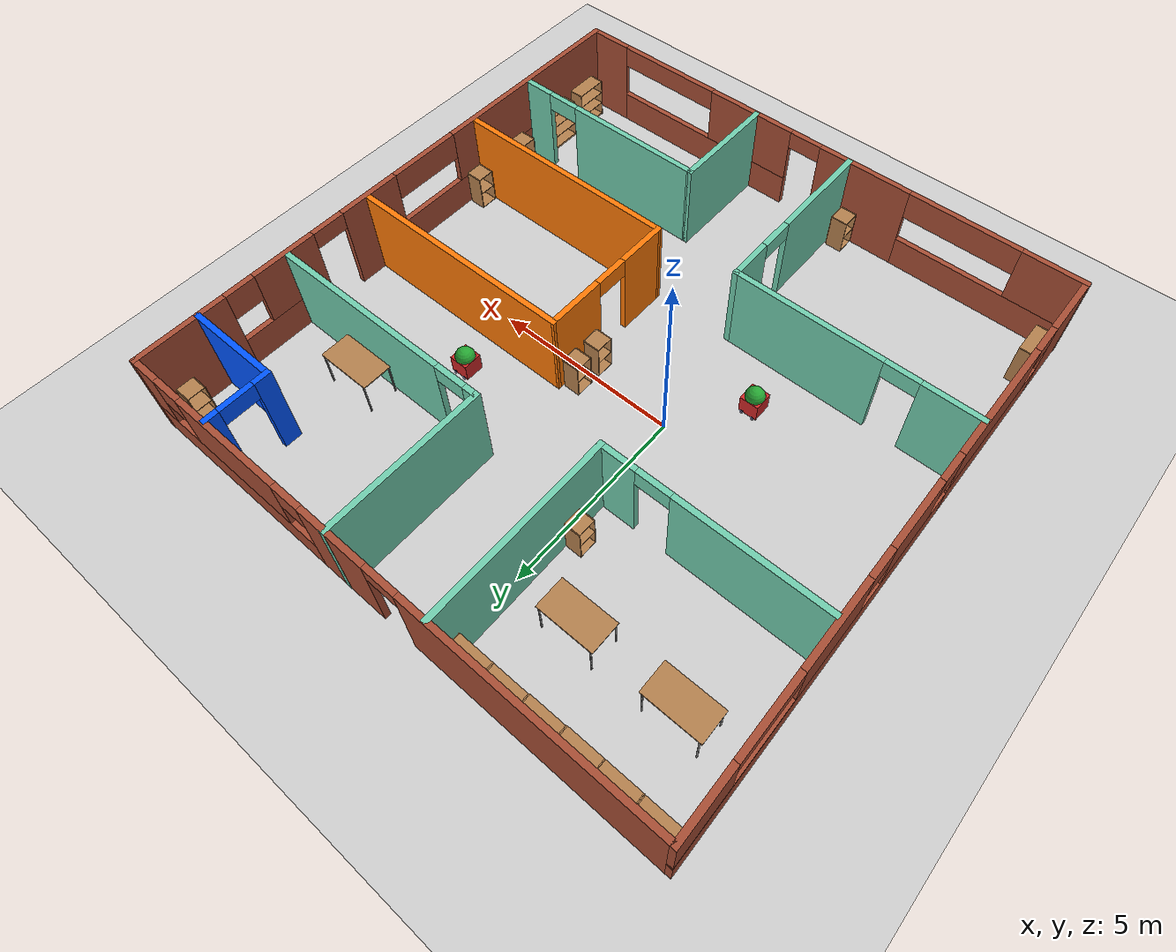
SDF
<sdf version="1.6">
 <world name="default">
  <plugin name="welcome" filename="libwelcome.so"/>
  <light name="sun" type="directional">
   <pose>0 0 10 0 -0 0</pose>
   <diffuse>0.8 0.8 0.8 1</diffuse>
   <specular>0.2 0.2 0.2 1</specular>
   <attenuation>
    <range>1000</range>
    <constant>0.9</constant>
    <linear>0.01</linear>
    <quadratic>0.001</quadratic>
   </attenuation>
   <direction>-0.5 0.1 -0.9</direction>
  </light>
  <model name="ground_plane">
   <static>1</static>
   <link name="link">
    <collision name="collision">
     <geometry><plane><normal>0 0 1</normal><size>100 100</size></plane></geometry>
     <surface><friction><ode><mu>100</mu><mu2>50</mu2></ode></friction></surface>
    </collision>
    <visual name="visual">
     <cast_shadows>0</cast_shadows>
     <geometry><plane><normal>0 0 1</normal><size>100 100</size></plane></geometry>
     <material>
      <script><uri>file://media/materials/scripts/gazebo.material</uri><name>Gazebo/Grey</name></script>
     </material>
    </visual>
   </link>
  </model>
  <gravity>0 0 -9.8</gravity>
  <magnetic_field>6e-06 2.3e-05 -4.2e-05</magnetic_field>
  <atmosphere type="adiabatic"/>
  <physics name="default_physics" default="0" type="ode">
   <max_step_size>0.001</max_step_size>
   <real_time_factor>1</real_time_factor>
   <real_time_update_rate>1000</real_time_update_rate>
  </physics>
  <scene><ambient>0.4 0.4 0.4 1</ambient><background>0.7 0.7 0.7 1</background><shadows>1</shadows></scene>
  <spherical_coordinates>
   <surface_model>EARTH_WGS84</surface_model>
   <latitude_deg>0</latitude_deg>
   <longitude_deg>0</longitude_deg>
   <elevation>0</elevation>
   <heading_deg>0</heading_deg>
  </spherical_coordinates>
  <model name="brickhouse">
   <pose>1.50992 -0.31487 0 0 -0 0</pose>
   <link name="Wall_18">
    <pose>-0.025 7.62202 0 0 -0 0</pose>
    <visual name="Wall_18_Visual_0">
     <pose>-4.1928 0 1.25 0 -0 0</pose>
     <geometry><box><size>6.6144 0.15 2.5</size></box></geometry>
     <material>
      <script><uri>file://media/materials/scripts/gazebo.material</uri><name>Gazebo/Bricks</name></script>
      <ambient>0.666667 0 0 1</ambient>
     </material>
     <meta><layer>0</layer></meta>
    </visual>
    <collision name="Wall_18_Collision_0">
     <geometry><box><size>6.6144 0.15 2.5</size></box></geometry>
     <pose>-4.1928 0 1.25 0 -0 0</pose>
    </collision>
    <visual name="Wall_18_Visual_1">
     <pose>0.9547 0 1.25 0 -0 0</pose>
     <geometry><box><size>1.8806 0.15 2.5</size></box></geometry>
     <material>
      <script><uri>file://media/materials/scripts/gazebo.material</uri><name>Gazebo/Bricks</name></script>
      <ambient>0.666667 0 0 1</ambient>
     </material>
     <meta><layer>0</layer></meta>
    </visual>
    <collision name="Wall_18_Collision_1">
     <geometry><box><size>1.8806 0.15 2.5</size></box></geometry>
     <pose>0.9547 0 1.25 0 -0 0</pose>
    </collision>
    <visual name="Wall_18_Visual_2">
     <pose>4.6975 0 0.45 0 -0 0</pose>
     <geometry><box><size>5.605 0.15 0.9</size></box></geometry>
     <material>
      <script><uri>file://media/materials/scripts/gazebo.material</uri><name>Gazebo/Bricks</name></script>
      <ambient>0.666667 0 0 1</ambient>
     </material>
     <meta><layer>0</layer></meta>
    </visual>
    <collision name="Wall_18_Collision_2">
     <geometry><box><size>5.605 0.15 0.9</size></box></geometry>
     <pose>4.6975 0 0.45 0 -0 0</pose>
    </collision>
    <visual name="Wall_18_Visual_3">
     <pose>4.27 0 1.7 0 -0 0</pose>
     <geometry><box><size>3.15 0.15 1.6</size></box></geometry>
     <material>
      <script><uri>file://media/materials/scripts/gazebo.material</uri><name>Gazebo/Bricks</name></script>
      <ambient>0.666667 0 0 1</ambient>
     </material>
     <meta><layer>0</layer></meta>
    </visual>
    <collision name="Wall_18_Collision_3">
     <geometry><box><size>3.15 0.15 1.6</size></box></geometry>
     <pose>4.27 0 1.7 0 -0 0</pose>
    </collision>
    <visual name="Wall_18_Visual_4">
     <pose>7.0725 0 1.7 0 -0 0</pose>
     <geometry><box><size>0.855 0.15 1.6</size></box></geometry>
     <material>
      <script><uri>file://media/materials/scripts/gazebo.material</uri><name>Gazebo/Bricks</name></script>
      <ambient>0.666667 0 0 1</ambient>
     </material>
     <meta><layer>0</layer></meta>
    </visual>
    <collision name="Wall_18_Collision_4">
     <geometry><box><size>0.855 0.15 1.6</size></box></geometry>
     <pose>7.0725 0 1.7 0 -0 0</pose>
    </collision>
    <visual name="Wall_18_Visual_5">
     <pose>2.295 0 2.1 0 -0 0</pose>
     <geometry><box><size>0.8 0.15 0.8</size></box></geometry>
     <material>
      <script><uri>file://media/materials/scripts/gazebo.material</uri><name>Gazebo/Bricks</name></script>
      <ambient>0.666667 0 0 1</ambient>
     </material>
     <meta><layer>0</layer></meta>
    </visual>
    <collision name="Wall_18_Collision_5">
     <geometry><box><size>0.8 0.15 0.8</size></box></geometry>
     <pose>2.295 0 2.1 0 -0 0</pose>
    </collision>
    <visual name="Wall_18_Visual_6">
     <pose>6.245 0 2.1 0 -0 0</pose>
     <geometry><box><size>0.8 0.15 0.8</size></box></geometry>
     <material>
      <script><uri>file://media/materials/scripts/gazebo.material</uri><name>Gazebo/Bricks</name></script>
      <ambient>0.666667 0 0 1</ambient>
     </material>
     <meta><layer>0</layer></meta>
    </visual>
    <collision name="Wall_18_Collision_6">
     <geometry><box><size>0.8 0.15 0.8</size></box></geometry>
     <pose>6.245 0 2.1 0 -0 0</pose>
    </collision>
    <visual name="Wall_18_Visual_7">
     <pose>-0.4356 0 2.25 0 -0 0</pose>
     <geometry><box><size>0.9 0.15 0.5</size></box></geometry>
     <material>
      <script><uri>file://media/materials/scripts/gazebo.material</uri><name>Gazebo/Bricks</name></script>
      <ambient>0.666667 0 0 1</ambient>
     </material>
     <meta><layer>0</layer></meta>
    </visual>
    <collision name="Wall_18_Collision_7">
     <geometry><box><size>0.9 0.15 0.5</size></box></geometry>
     <pose>-0.4356 0 2.25 0 -0 0</pose>
    </collision>
   </link>
   <link name="Wall_19">
    <pose>7.4 -0.001479 0 0 0 -1.5708</pose>
    <visual name="Wall_19_Visual_0">
     <pose>-6.48752 0 1.25 0 -0 0</pose>
     <geometry><box><size>2.42204 0.15 2.5</size></box></geometry>
     <material>
      <script><uri>file://media/materials/scripts/gazebo.material</uri><name>Gazebo/Bricks</name></script>
      <ambient>0.666667 0 0 1</ambient>
     </material>
     <meta><layer>0</layer></meta>
    </visual>
    <collision name="Wall_19_Collision_0">
     <geometry><box><size>2.42204 0.15 2.5</size></box></geometry>
     <pose>-6.48752 0 1.25 0 -0 0</pose>
    </collision>
    <visual name="Wall_19_Visual_1">
     <pose>-0.9765 0 1.25 0 -0 0</pose>
     <geometry><box><size>1.72 0.15 2.5</size></box></geometry>
     <material>
      <script><uri>file://media/materials/scripts/gazebo.material</uri><name>Gazebo/Bricks</name></script>
      <ambient>0.666667 0 0 1</ambient>
     </material>
     <meta><layer>0</layer></meta>
    </visual>
    <collision name="Wall_19_Collision_1">
     <geometry><box><size>1.72 0.15 2.5</size></box></geometry>
     <pose>-0.9765 0 1.25 0 -0 0</pose>
    </collision>
    <visual name="Wall_19_Visual_2">
     <pose>-4.0065 0 0.45 0 -0 0</pose>
     <geometry><box><size>2.54 0.15 0.9</size></box></geometry>
     <material>
      <script><uri>file://media/materials/scripts/gazebo.material</uri><name>Gazebo/Bricks</name></script>
      <ambient>0.666667 0 0 1</ambient>
     </material>
     <meta><layer>0</layer></meta>
    </visual>
    <collision name="Wall_19_Collision_2">
     <geometry><box><size>2.54 0.15 0.9</size></box></geometry>
     <pose>-4.0065 0 0.45 0 -0 0</pose>
    </collision>
    <visual name="Wall_19_Visual_3">
     <pose>3.79102 0 0.45 0 -0 0</pose>
     <geometry><box><size>7.81504 0.15 0.9</size></box></geometry>
     <material>
      <script><uri>file://media/materials/scripts/gazebo.material</uri><name>Gazebo/Bricks</name></script>
      <ambient>0.666667 0 0 1</ambient>
     </material>
     <meta><layer>0</layer></meta>
    </visual>
    <collision name="Wall_19_Collision_3">
     <geometry><box><size>7.81504 0.15 0.9</size></box></geometry>
     <pose>3.79102 0 0.45 0 -0 0</pose>
    </collision>
    <visual name="Wall_19_Visual_4">
     <pose>-3.6065 0 1.7 0 -0 0</pose>
     <geometry><box><size>1.74 0.15 1.6</size></box></geometry>
     <material>
      <script><uri>file://media/materials/scripts/gazebo.material</uri><name>Gazebo/Bricks</name></script>
      <ambient>0.666667 0 0 1</ambient>
     </material>
     <meta><layer>0</layer></meta>
    </visual>
    <collision name="Wall_19_Collision_4">
     <geometry><box><size>1.74 0.15 1.6</size></box></geometry>
     <pose>-3.6065 0 1.7 0 -0 0</pose>
    </collision>
    <visual name="Wall_19_Visual_5">
     <pose>-3.6065 0 1.7 0 -0 0</pose>
     <geometry><box><size>1.74 0.15 1.6</size></box></geometry>
     <material>
      <script><uri>file://media/materials/scripts/gazebo.material</uri><name>Gazebo/Bricks</name></script>
      <ambient>0.666667 0 0 1</ambient>
     </material>
     <meta><layer>0</layer></meta>
    </visual>
    <collision name="Wall_19_Collision_5">
     <geometry><box><size>1.74 0.15 1.6</size></box></geometry>
     <pose>-3.6065 0 1.7 0 -0 0</pose>
    </collision>
    <visual name="Wall_19_Visual_6">
     <pose>4.79102 0 1.7 0 -0 0</pose>
     <geometry><box><size>5.81504 0.15 1.6</size></box></geometry>
     <material>
      <script><uri>file://media/materials/scripts/gazebo.material</uri><name>Gazebo/Bricks</name></script>
      <ambient>0.666667 0 0 1</ambient>
     </material>
     <meta><layer>0</layer></meta>
    </visual>
    <collision name="Wall_19_Collision_6">
     <geometry><box><size>5.81504 0.15 1.6</size></box></geometry>
     <pose>4.79102 0 1.7 0 -0 0</pose>
    </collision>
    <visual name="Wall_19_Visual_7">
     <pose>-4.8765 0 2.1 0 -0 0</pose>
     <geometry><box><size>0.8 0.15 0.8</size></box></geometry>
     <material>
      <script><uri>file://media/materials/scripts/gazebo.material</uri><name>Gazebo/Bricks</name></script>
      <ambient>0.666667 0 0 1</ambient>
     </material>
     <meta><layer>0</layer></meta>
    </visual>
    <collision name="Wall_19_Collision_7">
     <geometry><box><size>0.8 0.15 0.8</size></box></geometry>
     <pose>-4.8765 0 2.1 0 -0 0</pose>
    </collision>
    <visual name="Wall_19_Visual_8">
     <pose>0.8835 0 2.1 0 -0 0</pose>
     <geometry><box><size>2 0.15 0.8</size></box></geometry>
     <material>
      <script><uri>file://media/materials/scripts/gazebo.material</uri><name>Gazebo/Bricks</name></script>
      <ambient>0.666667 0 0 1</ambient>
     </material>
     <meta><layer>0</layer></meta>
    </visual>
    <collision name="Wall_19_Collision_8">
     <geometry><box><size>2 0.15 0.8</size></box></geometry>
     <pose>0.8835 0 2.1 0 -0 0</pose>
    </collision>
    <visual name="Wall_19_Visual_9">
     <pose>-2.2865 0 2.25 0 -0 0</pose>
     <geometry><box><size>0.9 0.15 0.5</size></box></geometry>
     <material>
      <script><uri>file://media/materials/scripts/gazebo.material</uri><name>Gazebo/Bricks</name></script>
      <ambient>0.666667 0 0 1</ambient>
     </material>
     <meta><layer>0</layer></meta>
    </visual>
    <collision name="Wall_19_Collision_9">
     <geometry><box><size>0.9 0.15 0.5</size></box></geometry>
     <pose>-2.2865 0 2.25 0 -0 0</pose>
    </collision>
    <visual name="Wall_19_Visual_10">
     <pose>-2.2865 0 2.25 0 -0 0</pose>
     <geometry><box><size>0.9 0.15 0.5</size></box></geometry>
     <material>
      <script><uri>file://media/materials/scripts/gazebo.material</uri><name>Gazebo/Bricks</name></script>
      <ambient>0.666667 0 0 1</ambient>
     </material>
     <meta><layer>0</layer></meta>
    </visual>
    <collision name="Wall_19_Collision_10">
     <geometry><box><size>0.9 0.15 0.5</size></box></geometry>
     <pose>-2.2865 0 2.25 0 -0 0</pose>
    </collision>
   </link>
   <link name="Wall_20">
    <pose>-0.035 -7.62498 0 0 -0 3.14159</pose>
    <visual name="Wall_20_Visual_0">
     <pose>-6.8775 0 1.25 0 -0 0</pose>
     <geometry><box><size>1.245 0.15 2.5</size></box></geometry>
     <material>
      <script><uri>file://media/materials/scripts/gazebo.material</uri><name>Gazebo/Bricks</name></script>
      <ambient>0.666667 0 0 1</ambient>
     </material>
     <meta><layer>0</layer></meta>
    </visual>
    <collision name="Wall_20_Collision_0">
     <geometry><box><size>1.245 0.15 2.5</size></box></geometry>
     <pose>-6.8775 0 1.25 0 -0 0</pose>
    </collision>
    <visual name="Wall_20_Visual_1">
     <pose>1.515 0 1.25 0 -0 0</pose>
     <geometry><box><size>2.62 0.15 2.5</size></box></geometry>
     <material>
      <script><uri>file://media/materials/scripts/gazebo.material</uri><name>Gazebo/Bricks</name></script>
      <ambient>0.666667 0 0 1</ambient>
     </material>
     <meta><layer>0</layer></meta>
    </visual>
    <collision name="Wall_20_Collision_1">
     <geometry><box><size>2.62 0.15 2.5</size></box></geometry>
     <pose>1.515 0 1.25 0 -0 0</pose>
    </collision>
    <visual name="Wall_20_Visual_2">
     <pose>-3.475 0 0.45 0 -0 0</pose>
     <geometry><box><size>5.56 0.15 0.9</size></box></geometry>
     <material>
      <script><uri>file://media/materials/scripts/gazebo.material</uri><name>Gazebo/Bricks</name></script>
      <ambient>0.666667 0 0 1</ambient>
     </material>
     <meta><layer>0</layer></meta>
    </visual>
    <collision name="Wall_20_Collision_2">
     <geometry><box><size>5.56 0.15 0.9</size></box></geometry>
     <pose>-3.475 0 0.45 0 -0 0</pose>
    </collision>
    <visual name="Wall_20_Visual_3">
     <pose>5.1625 0 0.45 0 -0 0</pose>
     <geometry><box><size>4.675 0.15 0.9</size></box></geometry>
     <material>
      <script><uri>file://media/materials/scripts/gazebo.material</uri><name>Gazebo/Bricks</name></script>
      <ambient>0.666667 0 0 1</ambient>
     </material>
     <meta><layer>0</layer></meta>
    </visual>
    <collision name="Wall_20_Collision_3">
     <geometry><box><size>4.675 0.15 0.9</size></box></geometry>
     <pose>5.1625 0 0.45 0 -0 0</pose>
    </collision>
    <visual name="Wall_20_Visual_4">
     <pose>-1.975 0 1.7 0 -0 0</pose>
     <geometry><box><size>2.56 0.15 1.6</size></box></geometry>
     <material>
      <script><uri>file://media/materials/scripts/gazebo.material</uri><name>Gazebo/Bricks</name></script>
      <ambient>0.666667 0 0 1</ambient>
     </material>
     <meta><layer>0</layer></meta>
    </visual>
    <collision name="Wall_20_Collision_4">
     <geometry><box><size>2.56 0.15 1.6</size></box></geometry>
     <pose>-1.975 0 1.7 0 -0 0</pose>
    </collision>
    <visual name="Wall_20_Visual_5">
     <pose>-1.975 0 1.7 0 -0 0</pose>
     <geometry><box><size>2.56 0.15 1.6</size></box></geometry>
     <material>
      <script><uri>file://media/materials/scripts/gazebo.material</uri><name>Gazebo/Bricks</name></script>
      <ambient>0.666667 0 0 1</ambient>
     </material>
     <meta><layer>0</layer></meta>
    </visual>
    <collision name="Wall_20_Collision_5">
     <geometry><box><size>2.56 0.15 1.6</size></box></geometry>
     <pose>-1.975 0 1.7 0 -0 0</pose>
    </collision>
    <visual name="Wall_20_Visual_6">
     <pose>6.6625 0 1.7 0 -0 0</pose>
     <geometry><box><size>1.675 0.15 1.6</size></box></geometry>
     <material>
      <script><uri>file://media/materials/scripts/gazebo.material</uri><name>Gazebo/Bricks</name></script>
      <ambient>0.666667 0 0 1</ambient>
     </material>
     <meta><layer>0</layer></meta>
    </visual>
    <collision name="Wall_20_Collision_6">
     <geometry><box><size>1.675 0.15 1.6</size></box></geometry>
     <pose>6.6625 0 1.7 0 -0 0</pose>
    </collision>
    <visual name="Wall_20_Visual_7">
     <pose>4.325 0 2.1 0 -0 0</pose>
     <geometry><box><size>3 0.15 0.8</size></box></geometry>
     <material>
      <script><uri>file://media/materials/scripts/gazebo.material</uri><name>Gazebo/Bricks</name></script>
      <ambient>0.666667 0 0 1</ambient>
     </material>
     <meta><layer>0</layer></meta>
    </visual>
    <collision name="Wall_20_Collision_7">
     <geometry><box><size>3 0.15 0.8</size></box></geometry>
     <pose>4.325 0 2.1 0 -0 0</pose>
    </collision>
    <visual name="Wall_20_Visual_8">
     <pose>-4.755 0 2.2 0 -0 0</pose>
     <geometry><box><size>3 0.15 0.6</size></box></geometry>
     <material>
      <script><uri>file://media/materials/scripts/gazebo.material</uri><name>Gazebo/Bricks</name></script>
      <ambient>0.666667 0 0 1</ambient>
     </material>
     <meta><layer>0</layer></meta>
    </visual>
    <collision name="Wall_20_Collision_8">
     <geometry><box><size>3 0.15 0.6</size></box></geometry>
     <pose>-4.755 0 2.2 0 -0 0</pose>
    </collision>
    <visual name="Wall_20_Visual_9">
     <pose>-0.245 0 2.25 0 -0 0</pose>
     <geometry><box><size>0.9 0.15 0.5</size></box></geometry>
     <material>
      <script><uri>file://media/materials/scripts/gazebo.material</uri><name>Gazebo/Bricks</name></script>
      <ambient>0.666667 0 0 1</ambient>
     </material>
     <meta><layer>0</layer></meta>
    </visual>
    <collision name="Wall_20_Collision_9">
     <geometry><box><size>0.9 0.15 0.5</size></box></geometry>
     <pose>-0.245 0 2.25 0 -0 0</pose>
    </collision>
    <visual name="Wall_20_Visual_10">
     <pose>-0.245 0 2.25 0 -0 0</pose>
     <geometry><box><size>0.9 0.15 0.5</size></box></geometry>
     <material>
      <script><uri>file://media/materials/scripts/gazebo.material</uri><name>Gazebo/Bricks</name></script>
      <ambient>0.666667 0 0 1</ambient>
     </material>
     <meta><layer>0</layer></meta>
    </visual>
    <collision name="Wall_20_Collision_10">
     <geometry><box><size>0.9 0.15 0.5</size></box></geometry>
     <pose>-0.245 0 2.25 0 -0 0</pose>
    </collision>
   </link>
   <link name="Wall_21">
    <pose>-7.45 -0.001479 0 0 -0 1.5708</pose>
    <visual name="Wall_21_Visual_0">
     <pose>-6.82602 0 1.25 0 -0 0</pose>
     <geometry><box><size>1.74504 0.15 2.5</size></box></geometry>
     <material>
      <script><uri>file://media/materials/scripts/gazebo.material</uri><name>Gazebo/Bricks</name></script>
      <ambient>0.666667 0 0 1</ambient>
     </material>
     <meta><layer>0</layer></meta>
    </visual>
    <collision name="Wall_21_Collision_0">
     <geometry><box><size>1.74504 0.15 2.5</size></box></geometry>
     <pose>-6.82602 0 1.25 0 -0 0</pose>
    </collision>
    <visual name="Wall_21_Visual_1">
     <pose>-3.8585 0 0.5 0 -0 0</pose>
     <geometry><box><size>4.19 0.15 1</size></box></geometry>
     <material>
      <script><uri>file://media/materials/scripts/gazebo.material</uri><name>Gazebo/Bricks</name></script>
      <ambient>0.666667 0 0 1</ambient>
     </material>
     <meta><layer>0</layer></meta>
    </visual>
    <collision name="Wall_21_Collision_1">
     <geometry><box><size>4.19 0.15 1</size></box></geometry>
     <pose>-3.8585 0 0.5 0 -0 0</pose>
    </collision>
    <visual name="Wall_21_Visual_2">
     <pose>2.96752 0 0.45 0 -0 0</pose>
     <geometry><box><size>9.46204 0.15 0.9</size></box></geometry>
     <material>
      <script><uri>file://media/materials/scripts/gazebo.material</uri><name>Gazebo/Bricks</name></script>
      <ambient>0.666667 0 0 1</ambient>
     </material>
     <meta><layer>0</layer></meta>
    </visual>
    <collision name="Wall_21_Collision_2">
     <geometry><box><size>9.46204 0.15 0.9</size></box></geometry>
     <pose>2.96752 0 0.45 0 -0 0</pose>
    </collision>
    <visual name="Wall_21_Visual_3">
     <pose>-0.0185 0 1.7 0 -0 0</pose>
     <geometry><box><size>1.89 0.15 1.6</size></box></geometry>
     <material>
      <script><uri>file://media/materials/scripts/gazebo.material</uri><name>Gazebo/Bricks</name></script>
      <ambient>0.666667 0 0 1</ambient>
     </material>
     <meta><layer>0</layer></meta>
    </visual>
    <collision name="Wall_21_Collision_3">
     <geometry><box><size>1.89 0.15 1.6</size></box></geometry>
     <pose>-0.0185 0 1.7 0 -0 0</pose>
    </collision>
    <visual name="Wall_21_Visual_4">
     <pose>2.8565 0 1.7 0 -0 0</pose>
     <geometry><box><size>2.26 0.15 1.6</size></box></geometry>
     <material>
      <script><uri>file://media/materials/scripts/gazebo.material</uri><name>Gazebo/Bricks</name></script>
      <ambient>0.666667 0 0 1</ambient>
     </material>
     <meta><layer>0</layer></meta>
    </visual>
    <collision name="Wall_21_Collision_4">
     <geometry><box><size>2.26 0.15 1.6</size></box></geometry>
     <pose>2.8565 0 1.7 0 -0 0</pose>
    </collision>
    <visual name="Wall_21_Visual_5">
     <pose>5.84252 0 0.95 0 -0 0</pose>
     <geometry><box><size>3.71204 0.15 0.1</size></box></geometry>
     <material>
      <script><uri>file://media/materials/scripts/gazebo.material</uri><name>Gazebo/Bricks</name></script>
      <ambient>0.666667 0 0 1</ambient>
     </material>
     <meta><layer>0</layer></meta>
    </visual>
    <collision name="Wall_21_Collision_5">
     <geometry><box><size>3.71204 0.15 0.1</size></box></geometry>
     <pose>5.84252 0 0.95 0 -0 0</pose>
    </collision>
    <visual name="Wall_21_Visual_6">
     <pose>6.84252 0 1.75 0 -0 0</pose>
     <geometry><box><size>1.71204 0.15 1.5</size></box></geometry>
     <material>
      <script><uri>file://media/materials/scripts/gazebo.material</uri><name>Gazebo/Bricks</name></script>
      <ambient>0.666667 0 0 1</ambient>
     </material>
     <meta><layer>0</layer></meta>
    </visual>
    <collision name="Wall_21_Collision_6">
     <geometry><box><size>1.71204 0.15 1.5</size></box></geometry>
     <pose>6.84252 0 1.75 0 -0 0</pose>
    </collision>
    <visual name="Wall_21_Visual_7">
     <pose>-3.4585 0 1.75 0 -0 0</pose>
     <geometry><box><size>3.39 0.15 1.5</size></box></geometry>
     <material>
      <script><uri>file://media/materials/scripts/gazebo.material</uri><name>Gazebo/Bricks</name></script>
      <ambient>0.666667 0 0 1</ambient>
     </material>
     <meta><layer>0</layer></meta>
    </visual>
    <collision name="Wall_21_Collision_7">
     <geometry><box><size>3.39 0.15 1.5</size></box></geometry>
     <pose>-3.4585 0 1.75 0 -0 0</pose>
    </collision>
    <visual name="Wall_21_Visual_8">
     <pose>-3.4585 0 1.75 0 -0 0</pose>
     <geometry><box><size>3.39 0.15 1.5</size></box></geometry>
     <material>
      <script><uri>file://media/materials/scripts/gazebo.material</uri><name>Gazebo/Bricks</name></script>
      <ambient>0.666667 0 0 1</ambient>
     </material>
     <meta><layer>0</layer></meta>
    </visual>
    <collision name="Wall_21_Collision_8">
     <geometry><box><size>3.39 0.15 1.5</size></box></geometry>
     <pose>-3.4585 0 1.75 0 -0 0</pose>
    </collision>
    <visual name="Wall_21_Visual_9">
     <pose>1.3265 0 2.1 0 -0 0</pose>
     <geometry><box><size>0.8 0.15 0.8</size></box></geometry>
     <material>
      <script><uri>file://media/materials/scripts/gazebo.material</uri><name>Gazebo/Bricks</name></script>
      <ambient>0.666667 0 0 1</ambient>
     </material>
     <meta><layer>0</layer></meta>
    </visual>
    <collision name="Wall_21_Collision_9">
     <geometry><box><size>0.8 0.15 0.8</size></box></geometry>
     <pose>1.3265 0 2.1 0 -0 0</pose>
    </collision>
    <visual name="Wall_21_Visual_10">
     <pose>-1.3635 0 2.1 0 -0 0</pose>
     <geometry><box><size>0.8 0.15 0.8</size></box></geometry>
     <material>
      <script><uri>file://media/materials/scripts/gazebo.material</uri><name>Gazebo/Bricks</name></script>
      <ambient>0.666667 0 0 1</ambient>
     </material>
     <meta><layer>0</layer></meta>
    </visual>
    <collision name="Wall_21_Collision_10">
     <geometry><box><size>0.8 0.15 0.8</size></box></geometry>
     <pose>-1.3635 0 2.1 0 -0 0</pose>
    </collision>
    <visual name="Wall_21_Visual_11">
     <pose>-1.3635 0 2.1 0 -0 0</pose>
     <geometry><box><size>0.8 0.15 0.8</size></box></geometry>
     <material>
      <script><uri>file://media/materials/scripts/gazebo.material</uri><name>Gazebo/Bricks</name></script>
      <ambient>0.666667 0 0 1</ambient>
     </material>
     <meta><layer>0</layer></meta>
    </visual>
    <collision name="Wall_21_Collision_11">
     <geometry><box><size>0.8 0.15 0.8</size></box></geometry>
     <pose>-1.3635 0 2.1 0 -0 0</pose>
    </collision>
    <visual name="Wall_21_Visual_12">
     <pose>-5.5535 0 2.15 0 -0 0</pose>
     <geometry><box><size>0.8 0.15 0.7</size></box></geometry>
     <material>
      <script><uri>file://media/materials/scripts/gazebo.material</uri><name>Gazebo/Bricks</name></script>
      <ambient>0.666667 0 0 1</ambient>
     </material>
     <meta><layer>0</layer></meta>
    </visual>
    <collision name="Wall_21_Collision_12">
     <geometry><box><size>0.8 0.15 0.7</size></box></geometry>
     <pose>-5.5535 0 2.15 0 -0 0</pose>
    </collision>
    <visual name="Wall_21_Visual_13">
     <pose>4.9865 0 2.25 0 -0 0</pose>
     <geometry><box><size>2 0.15 0.5</size></box></geometry>
     <material>
      <script><uri>file://media/materials/scripts/gazebo.material</uri><name>Gazebo/Bricks</name></script>
      <ambient>0.666667 0 0 1</ambient>
     </material>
     <meta><layer>0</layer></meta>
    </visual>
    <collision name="Wall_21_Collision_13">
     <geometry><box><size>2 0.15 0.5</size></box></geometry>
     <pose>4.9865 0 2.25 0 -0 0</pose>
    </collision>
   </link>
   <link name="Wall_23">
    <collision name="Wall_23_Collision">
     <geometry><box><size>4.25 0.15 2.5</size></box></geometry>
     <pose>0 0 1.25 0 -0 0</pose>
    </collision>
    <visual name="Wall_23_Visual">
     <pose>0 0 1.25 0 -0 0</pose>
     <geometry><box><size>4.25 0.15 2.5</size></box></geometry>
     <material>
      <script><uri>file://media/materials/scripts/gazebo.material</uri><name>Gazebo/Grey</name></script>
      <ambient>0.435294 0.796078 0.67451 1</ambient>
     </material>
     <meta><layer>0</layer></meta>
    </visual>
    <pose>1.11 5.57502 0 0 0 -1.5708</pose>
   </link>
   <link name="Wall_24">
    <pose>4.285 3.52502 0 0 -0 0</pose>
    <visual name="Wall_24_Visual_0">
     <pose>-3.0375 0 1.25 0 -0 0</pose>
     <geometry><box><size>0.425 0.15 2.5</size></box></geometry>
     <material>
      <script><uri>file://media/materials/scripts/gazebo.material</uri><name>Gazebo/Grey</name></script>
      <ambient>0.435294 0.796078 0.67451 1</ambient>
     </material>
     <meta><layer>0</layer></meta>
    </visual>
    <collision name="Wall_24_Collision_0">
     <geometry><box><size>0.425 0.15 2.5</size></box></geometry>
     <pose>-3.0375 0 1.25 0 -0 0</pose>
    </collision>
    <visual name="Wall_24_Visual_1">
     <pose>0.5625 0 1.25 0 -0 0</pose>
     <geometry><box><size>5.075 0.15 2.5</size></box></geometry>
     <material>
      <script><uri>file://media/materials/scripts/gazebo.material</uri><name>Gazebo/Grey</name></script>
      <ambient>0.435294 0.796078 0.67451 1</ambient>
     </material>
     <meta><layer>0</layer></meta>
    </visual>
    <collision name="Wall_24_Collision_1">
     <geometry><box><size>5.075 0.15 2.5</size></box></geometry>
     <pose>0.5625 0 1.25 0 -0 0</pose>
    </collision>
    <visual name="Wall_24_Visual_2">
     <pose>-2.375 0 2.25 0 -0 0</pose>
     <geometry><box><size>0.9 0.15 0.5</size></box></geometry>
     <material>
      <script><uri>file://media/materials/scripts/gazebo.material</uri><name>Gazebo/Grey</name></script>
      <ambient>0.435294 0.796078 0.67451 1</ambient>
     </material>
     <meta><layer>0</layer></meta>
    </visual>
    <collision name="Wall_24_Collision_2">
     <geometry><box><size>0.9 0.15 0.5</size></box></geometry>
     <pose>-2.375 0 2.25 0 -0 0</pose>
    </collision>
   </link>
   <link name="Wall_26">
    <pose>4.95 6.78502 0 0 0 -1.5708</pose>
    <visual name="Wall_26_Visual_0">
     <pose>-0.6775 0 1.25 0 -0 0</pose>
     <geometry><box><size>0.395 0.15 2.5</size></box></geometry>
     <material>
      <script><uri>file://media/materials/scripts/gazebo.material</uri><name>Gazebo/Grey</name></script>
      <ambient>0 0.333333 1 1</ambient>
     </material>
     <meta><layer>0</layer></meta>
    </visual>
    <collision name="Wall_26_Collision_0">
     <geometry><box><size>0.395 0.15 2.5</size></box></geometry>
     <pose>-0.6775 0 1.25 0 -0 0</pose>
    </collision>
    <visual name="Wall_26_Visual_1">
     <pose>0.6475 0 1.25 0 -0 0</pose>
     <geometry><box><size>0.455 0.15 2.5</size></box></geometry>
     <material>
      <script><uri>file://media/materials/scripts/gazebo.material</uri><name>Gazebo/Grey</name></script>
      <ambient>0 0.333333 1 1</ambient>
     </material>
     <meta><layer>0</layer></meta>
    </visual>
    <collision name="Wall_26_Collision_1">
     <geometry><box><size>0.455 0.15 2.5</size></box></geometry>
     <pose>0.6475 0 1.25 0 -0 0</pose>
    </collision>
    <visual name="Wall_26_Visual_2">
     <pose>-0.03 0 2.25 0 -0 0</pose>
     <geometry><box><size>0.9 0.15 0.5</size></box></geometry>
     <material>
      <script><uri>file://media/materials/scripts/gazebo.material</uri><name>Gazebo/Grey</name></script>
      <ambient>0 0.333333 1 1</ambient>
     </material>
     <meta><layer>0</layer></meta>
    </visual>
    <collision name="Wall_26_Collision_2">
     <geometry><box><size>0.9 0.15 0.5</size></box></geometry>
     <pose>-0.03 0 2.25 0 -0 0</pose>
    </collision>
   </link>
   <link name="Wall_27">
    <collision name="Wall_27_Collision">
     <geometry><box><size>2.51 0.15 2.5</size></box></geometry>
     <pose>0 0 1.25 0 -0 0</pose>
    </collision>
    <visual name="Wall_27_Visual">
     <pose>0 0 1.25 0 -0 0</pose>
     <geometry><box><size>2.51 0.15 2.5</size></box></geometry>
     <material>
      <script><uri>file://media/materials/scripts/gazebo.material</uri><name>Gazebo/Grey</name></script>
      <ambient>0 0.333333 1 1</ambient>
     </material>
     <meta><layer>0</layer></meta>
    </visual>
    <pose>6.19 5.98502 0 0 -0 0</pose>
   </link>
   <link name="Wall_29">
    <collision name="Wall_29_Collision">
     <geometry><box><size>3 0.15 2.5</size></box></geometry>
     <pose>0 0 1.25 0 -0 0</pose>
    </collision>
    <visual name="Wall_29_Visual">
     <pose>0 0 1.25 0 -0 0</pose>
     <geometry><box><size>3 0.15 2.5</size></box></geometry>
     <material>
      <script><uri>file://media/materials/scripts/gazebo.material</uri><name>Gazebo/Grey</name></script>
      <ambient>0.435294 0.796078 0.67451 1</ambient>
     </material>
     <meta><layer>0</layer></meta>
    </visual>
    <pose>1.78 -6.16998 0 0 -0 1.5708</pose>
   </link>
   <link name="Wall_30">
    <pose>4.58 -4.74498 0 0 -0 0</pose>
    <visual name="Wall_30_Visual_0">
     <pose>-0.9275 0 1.25 0 -0 0</pose>
     <geometry><box><size>3.895 0.15 2.5</size></box></geometry>
     <material>
      <script><uri>file://media/materials/scripts/gazebo.material</uri><name>Gazebo/Grey</name></script>
      <ambient>0.435294 0.796078 0.67451 1</ambient>
     </material>
     <meta><layer>0</layer></meta>
    </visual>
    <collision name="Wall_30_Collision_0">
     <geometry><box><size>3.895 0.15 2.5</size></box></geometry>
     <pose>-0.9275 0 1.25 0 -0 0</pose>
    </collision>
    <visual name="Wall_30_Visual_1">
     <pose>2.3975 0 1.25 0 -0 0</pose>
     <geometry><box><size>0.955 0.15 2.5</size></box></geometry>
     <material>
      <script><uri>file://media/materials/scripts/gazebo.material</uri><name>Gazebo/Grey</name></script>
      <ambient>0.435294 0.796078 0.67451 1</ambient>
     </material>
     <meta><layer>0</layer></meta>
    </visual>
    <collision name="Wall_30_Collision_1">
     <geometry><box><size>0.955 0.15 2.5</size></box></geometry>
     <pose>2.3975 0 1.25 0 -0 0</pose>
    </collision>
    <visual name="Wall_30_Visual_2">
     <pose>1.47 0 2.25 0 -0 0</pose>
     <geometry><box><size>0.9 0.15 0.5</size></box></geometry>
     <material>
      <script><uri>file://media/materials/scripts/gazebo.material</uri><name>Gazebo/Grey</name></script>
      <ambient>0.435294 0.796078 0.67451 1</ambient>
     </material>
     <meta><layer>0</layer></meta>
    </visual>
    <collision name="Wall_30_Collision_2">
     <geometry><box><size>0.9 0.15 0.5</size></box></geometry>
     <pose>1.47 0 2.25 0 -0 0</pose>
    </collision>
   </link>
   <link name="Wall_32">
    <collision name="Wall_32_Collision">
     <geometry><box><size>6.25 0.15 2.5</size></box></geometry>
     <pose>0 0 1.25 0 -0 0</pose>
    </collision>
    <visual name="Wall_32_Visual">
     <pose>0 0 1.25 0 -0 0</pose>
     <geometry><box><size>6.25 0.15 2.5</size></box></geometry>
     <material>
      <script><uri>file://media/materials/scripts/gazebo.material</uri><name>Gazebo/Grey</name></script>
      <ambient>0.996078 0.47451 0.0196078 1</ambient>
     </material>
     <meta><layer>0</layer></meta>
    </visual>
    <pose>4.22 -2.67498 0 0 -0 3.14159</pose>
   </link>
   <link name="Wall_33">
    <pose>1.175 -0.819979 0 0 -0 1.5681</pose>
    <visual name="Wall_33_Visual_0">
     <pose>-1.23964 0 1.25 0 -0 0</pose>
     <geometry><box><size>1.38072 0.15 2.5</size></box></geometry>
     <material>
      <script><uri>file://media/materials/scripts/gazebo.material</uri><name>Gazebo/Grey</name></script>
      <ambient>0.996078 0.47451 0.0196078 1</ambient>
     </material>
     <meta><layer>0</layer></meta>
    </visual>
    <collision name="Wall_33_Collision_0">
     <geometry><box><size>1.38072 0.15 2.5</size></box></geometry>
     <pose>-1.23964 0 1.25 0 -0 0</pose>
    </collision>
    <visual name="Wall_33_Visual_1">
     <pose>1.14036 0 1.25 0 -0 0</pose>
     <geometry><box><size>1.57929 0.15 2.5</size></box></geometry>
     <material>
      <script><uri>file://media/materials/scripts/gazebo.material</uri><name>Gazebo/Grey</name></script>
      <ambient>0.996078 0.47451 0.0196078 1</ambient>
     </material>
     <meta><layer>0</layer></meta>
    </visual>
    <collision name="Wall_33_Collision_1">
     <geometry><box><size>1.57929 0.15 2.5</size></box></geometry>
     <pose>1.14036 0 1.25 0 -0 0</pose>
    </collision>
    <visual name="Wall_33_Visual_2">
     <pose>-0.099282 0 2.25 0 -0 0</pose>
     <geometry><box><size>0.9 0.15 0.5</size></box></geometry>
     <material>
      <script><uri>file://media/materials/scripts/gazebo.material</uri><name>Gazebo/Grey</name></script>
      <ambient>0.996078 0.47451 0.0196078 1</ambient>
     </material>
     <meta><layer>0</layer></meta>
    </visual>
    <collision name="Wall_33_Collision_2">
     <geometry><box><size>0.9 0.15 0.5</size></box></geometry>
     <pose>-0.099282 0 2.25 0 -0 0</pose>
    </collision>
   </link>
   <link name="Wall_34">
    <collision name="Wall_34_Collision">
     <geometry><box><size>6.36 0.15 2.5</size></box></geometry>
     <pose>0 0 1.25 0 -0 0</pose>
    </collision>
    <visual name="Wall_34_Visual">
     <pose>0 0 1.25 0 -0 0</pose>
     <geometry><box><size>6.36 0.15 2.5</size></box></geometry>
     <material>
      <script><uri>file://media/materials/scripts/gazebo.material</uri><name>Gazebo/Grey</name></script>
      <ambient>0.996078 0.47451 0.0196078 1</ambient>
     </material>
     <meta><layer>0</layer></meta>
    </visual>
    <pose>4.285 1.03502 0 0 -0 0</pose>
   </link>
   <link name="Wall_38">
    <pose>-1.09 -5.18998 0 0 -0 1.5708</pose>
    <visual name="Wall_38_Visual_0">
     <pose>-1.05018 0 1.25 0 -0 0</pose>
     <geometry><box><size>2.89963 0.15 2.5</size></box></geometry>
     <material>
      <script><uri>file://media/materials/scripts/gazebo.material</uri><name>Gazebo/Grey</name></script>
      <ambient>0.435294 0.796078 0.67451 1</ambient>
     </material>
     <meta><layer>0</layer></meta>
    </visual>
    <collision name="Wall_38_Collision_0">
     <geometry><box><size>2.89963 0.15 2.5</size></box></geometry>
     <pose>-1.05018 0 1.25 0 -0 0</pose>
    </collision>
    <visual name="Wall_38_Visual_1">
     <pose>1.89982 0 1.25 0 -0 0</pose>
     <geometry><box><size>1.20036 0.15 2.5</size></box></geometry>
     <material>
      <script><uri>file://media/materials/scripts/gazebo.material</uri><name>Gazebo/Grey</name></script>
      <ambient>0.435294 0.796078 0.67451 1</ambient>
     </material>
     <meta><layer>0</layer></meta>
    </visual>
    <collision name="Wall_38_Collision_1">
     <geometry><box><size>1.20036 0.15 2.5</size></box></geometry>
     <pose>1.89982 0 1.25 0 -0 0</pose>
    </collision>
    <visual name="Wall_38_Visual_2">
     <pose>0.849635 0 2.25 0 -0 0</pose>
     <geometry><box><size>0.9 0.15 0.5</size></box></geometry>
     <material>
      <script><uri>file://media/materials/scripts/gazebo.material</uri><name>Gazebo/Grey</name></script>
      <ambient>0.435294 0.796078 0.67451 1</ambient>
     </material>
     <meta><layer>0</layer></meta>
    </visual>
    <collision name="Wall_38_Collision_2">
     <geometry><box><size>0.9 0.15 0.5</size></box></geometry>
     <pose>0.849635 0 2.25 0 -0 0</pose>
    </collision>
   </link>
   <link name="Wall_39">
    <pose>-4.26 -2.76498 0 0 -0 3.14159</pose>
    <visual name="Wall_39_Visual_0">
     <pose>-1.23097 0 1.25 0 -0 0</pose>
     <geometry><box><size>4.02806 0.15 2.5</size></box></geometry>
     <material>
      <script><uri>file://media/materials/scripts/gazebo.material</uri><name>Gazebo/Grey</name></script>
      <ambient>0.435294 0.796078 0.67451 1</ambient>
     </material>
     <meta><layer>0</layer></meta>
    </visual>
    <collision name="Wall_39_Collision_0">
     <geometry><box><size>4.02806 0.15 2.5</size></box></geometry>
     <pose>-1.23097 0 1.25 0 -0 0</pose>
    </collision>
    <visual name="Wall_39_Visual_1">
     <pose>2.46403 0 1.25 0 -0 0</pose>
     <geometry><box><size>1.56194 0.15 2.5</size></box></geometry>
     <material>
      <script><uri>file://media/materials/scripts/gazebo.material</uri><name>Gazebo/Grey</name></script>
      <ambient>0.435294 0.796078 0.67451 1</ambient>
     </material>
     <meta><layer>0</layer></meta>
    </visual>
    <collision name="Wall_39_Collision_1">
     <geometry><box><size>1.56194 0.15 2.5</size></box></geometry>
     <pose>2.46403 0 1.25 0 -0 0</pose>
    </collision>
    <visual name="Wall_39_Visual_2">
     <pose>1.23306 0 2.25 0 -0 0</pose>
     <geometry><box><size>0.9 0.15 0.5</size></box></geometry>
     <material>
      <script><uri>file://media/materials/scripts/gazebo.material</uri><name>Gazebo/Grey</name></script>
      <ambient>0.435294 0.796078 0.67451 1</ambient>
     </material>
     <meta><layer>0</layer></meta>
    </visual>
    <collision name="Wall_39_Collision_2">
     <geometry><box><size>0.9 0.15 0.5</size></box></geometry>
     <pose>1.23306 0 2.25 0 -0 0</pose>
    </collision>
   </link>
   <link name="Wall_45">
    <collision name="Wall_45_Collision">
     <geometry><box><size>5 0.15 2.5</size></box></geometry>
     <pose>0 0 1.25 0 -0 0</pose>
    </collision>
    <visual name="Wall_45_Visual">
     <pose>0 0 1.25 0 -0 0</pose>
     <geometry><box><size>5 0.15 2.5</size></box></geometry>
     <material>
      <script><uri>file://media/materials/scripts/gazebo.material</uri><name>Gazebo/Grey</name></script>
      <ambient>0.435294 0.796078 0.67451 1</ambient>
     </material>
     <meta><layer>0</layer></meta>
    </visual>
    <pose>-1.7 5.18002 0 0 0 -1.5708</pose>
   </link>
   <link name="Wall_46">
    <pose>-4.515 2.75502 0 0 -0 3.14159</pose>
    <visual name="Wall_46_Visual_0">
     <pose>-2.3875 0 1.25 0 -0 0</pose>
     <geometry><box><size>1.025 0.15 2.5</size></box></geometry>
     <material>
      <script><uri>file://media/materials/scripts/gazebo.material</uri><name>Gazebo/Grey</name></script>
      <ambient>0.435294 0.796078 0.67451 1</ambient>
     </material>
     <meta><layer>0</layer></meta>
    </visual>
    <collision name="Wall_46_Collision_0">
     <geometry><box><size>1.025 0.15 2.5</size></box></geometry>
     <pose>-2.3875 0 1.25 0 -0 0</pose>
    </collision>
    <visual name="Wall_46_Visual_1">
     <pose>0.9625 0 1.25 0 -0 0</pose>
     <geometry><box><size>3.875 0.15 2.5</size></box></geometry>
     <material>
      <script><uri>file://media/materials/scripts/gazebo.material</uri><name>Gazebo/Grey</name></script>
      <ambient>0.435294 0.796078 0.67451 1</ambient>
     </material>
     <meta><layer>0</layer></meta>
    </visual>
    <collision name="Wall_46_Collision_1">
     <geometry><box><size>3.875 0.15 2.5</size></box></geometry>
     <pose>0.9625 0 1.25 0 -0 0</pose>
    </collision>
    <visual name="Wall_46_Visual_2">
     <pose>-1.425 0 2.25 0 -0 0</pose>
     <geometry><box><size>0.9 0.15 0.5</size></box></geometry>
     <material>
      <script><uri>file://media/materials/scripts/gazebo.material</uri><name>Gazebo/Grey</name></script>
      <ambient>0.435294 0.796078 0.67451 1</ambient>
     </material>
     <meta><layer>0</layer></meta>
    </visual>
    <collision name="Wall_46_Collision_2">
     <geometry><box><size>0.9 0.15 0.5</size></box></geometry>
     <pose>-1.425 0 2.25 0 -0 0</pose>
    </collision>
   </link>
   <static>1</static>
  </model>
  <model name="simplebot">
   <link name="robot_link">
    <pose>0 0 0.3 0 -0 0</pose>
    <inertial>
     <mass>1</mass>
     <inertia><ixx>1</ixx><ixy>0</ixy><ixz>0</ixz><iyy>1</iyy><iyz>0</iyz><izz>1</izz></inertia>
    </inertial>
    <visual name="head_visual">
     <pose>0 0 0.25 0 0 -2.5</pose>
     <geometry><sphere><radius>0.25</radius></sphere></geometry>
     <material>
      <shader type="pixel"><normal_map>__default__</normal_map></shader>
      <emissive>0 0 0 1</emissive>
      <ambient>0.3 0.3 0.3 1</ambient>
      <diffuse>0.7 0.7 0.7 1</diffuse>
      <specular>0.01 0.01 0.01 1</specular>
      <script><uri>file://media/materials/scripts/gazebo.material</uri><name>Gazebo/Green</name></script>
     </material>
    </visual>
    <visual name="body_visual">
     <geometry><box><size>0.5 0.5 0.5</size></box></geometry>
     <material>
      <shader type="pixel"><normal_map>__default__</normal_map></shader>
      <emissive>0 0 0 1</emissive>
      <ambient>1 0 0 1</ambient>
      <diffuse>1 0 0 1</diffuse>
      <specular>0.1 0.1 0.1 1</specular>
      <script><uri>file://media/materials/scripts/gazebo.material</uri><name>Gazebo/Red</name></script>
     </material>
    </visual>
    <visual name="power_led_visual">
     <pose>0.225 0.225 0.25 0 -0 0</pose>
     <geometry><sphere><radius>0.003</radius></sphere></geometry>
     <material>
      <ambient>0 0 0 1</ambient>
      <diffuse>0 0 0 1</diffuse>
      <specular>0 0 0 1</specular>
      <emissive>0 1 0 1</emissive>
     </material>
    </visual>
    <collision name="body_collision">
     <geometry><box><size>0.5 0.5 0.5</size></box></geometry>
     <surface>
      <friction>
       <ode><mu>1</mu><mu2>1</mu2><fdir1>0 0 0</fdir1><slip1>0</slip1><slip2>0</slip2></ode>
       <torsional>
        <coefficient>1</coefficient>
        <patch_radius>0</patch_radius>
        <surface_radius>0</surface_radius>
        <use_patch_radius>1</use_patch_radius>
        <ode><slip>0</slip></ode>
       </torsional>
      </friction>
      <bounce><restitution_coefficient>0</restitution_coefficient><threshold>1e+06</threshold></bounce>
      <contact>
       <collide_without_contact>0</collide_without_contact>
       <collide_without_contact_bitmask>1</collide_without_contact_bitmask>
       <collide_bitmask>1</collide_bitmask>
       <ode>
        <soft_cfm>0</soft_cfm>
        <soft_erp>0.2</soft_erp>
        <kp>1e+13</kp>
        <kd>1</kd>
        <max_vel>0.01</max_vel>
        <min_depth>0</min_depth>
       </ode>
       <bullet>
        <split_impulse>1</split_impulse>
        <split_impulse_penetration_threshold>-0.01</split_impulse_penetration_threshold>
        <soft_cfm>0</soft_cfm>
        <soft_erp>0.2</soft_erp>
        <kp>1e+13</kp>
        <kd>1</kd>
       </bullet>
      </contact>
     </surface>
    </collision>
   </link>
   <link name="wheel_1">
    <pose>0.15 -0.26 0.05 1.5707 -0 0</pose>
    <inertial>
     <mass>1</mass>
     <inertia><ixx>0.145833</ixx><ixy>0</ixy><ixz>0</ixz><iyy>0.145833</iyy><iyz>0</iyz><izz>0.125</izz></inertia>
    </inertial>
    <visual name="visual">
     <geometry><cylinder><radius>0.05</radius><length>0.02</length></cylinder></geometry>
     <material>
      <lighting>1</lighting>
      <script><uri>file://media/materials/scripts/gazebo.material</uri><name>Gazebo/Grey</name></script>
      <shader type="pixel"><normal_map>__default__</normal_map></shader>
      <ambient>0.1 0.1 0.1 1</ambient>
      <diffuse>0.1 0.1 0.2 1</diffuse>
      <specular>0.01 0.01 0.01 1</specular>
      <emissive>0 0 0 1</emissive>
     </material>
    </visual>
    <collision name="collision">
     <geometry><cylinder><radius>0.05</radius><length>0.02</length></cylinder></geometry>
     <surface>
      <friction>
       <ode><mu>1</mu><mu2>1</mu2><fdir1>0 0 0</fdir1><slip1>0</slip1><slip2>0</slip2></ode>
       <torsional>
        <coefficient>1</coefficient>
        <patch_radius>0</patch_radius>
        <surface_radius>0</surface_radius>
        <use_patch_radius>1</use_patch_radius>
        <ode><slip>0</slip></ode>
       </torsional>
      </friction>
      <bounce><restitution_coefficient>0</restitution_coefficient><threshold>1e+06</threshold></bounce>
      <contact>
       <collide_without_contact>0</collide_without_contact>
       <collide_without_contact_bitmask>1</collide_without_contact_bitmask>
       <collide_bitmask>1</collide_bitmask>
       <ode>
        <soft_cfm>0</soft_cfm>
        <soft_erp>0.2</soft_erp>
        <kp>1e+13</kp>
        <kd>1</kd>
        <max_vel>0.01</max_vel>
        <min_depth>0</min_depth>
       </ode>
       <bullet>
        <split_impulse>1</split_impulse>
        <split_impulse_penetration_threshold>-0.01</split_impulse_penetration_threshold>
        <soft_cfm>0</soft_cfm>
        <soft_erp>0.2</soft_erp>
        <kp>1e+13</kp>
        <kd>1</kd>
       </bullet>
      </contact>
     </surface>
    </collision>
   </link>
   <link name="wheel_2">
    <pose>0.15 0.26 0.05 1.5707 -0 0</pose>
    <inertial>
     <mass>1</mass>
     <inertia><ixx>0.145833</ixx><ixy>0</ixy><ixz>0</ixz><iyy>0.145833</iyy><iyz>0</iyz><izz>0.125</izz></inertia>
    </inertial>
    <visual name="visual">
     <geometry><cylinder><radius>0.05</radius><length>0.02</length></cylinder></geometry>
     <material>
      <lighting>1</lighting>
      <script><uri>file://media/materials/scripts/gazebo.material</uri><name>Gazebo/Grey</name></script>
      <shader type="pixel"><normal_map>__default__</normal_map></shader>
      <ambient>0.1 0.1 0.1 1</ambient>
      <diffuse>0.1 0.1 0.2 1</diffuse>
      <specular>0.01 0.01 0.01 1</specular>
      <emissive>0 0 0 1</emissive>
     </material>
    </visual>
    <collision name="collision">
     <geometry><cylinder><radius>0.05</radius><length>0.02</length></cylinder></geometry>
     <surface>
      <friction>
       <ode><mu>1</mu><mu2>1</mu2><fdir1>0 0 0</fdir1><slip1>0</slip1><slip2>0</slip2></ode>
       <torsional>
        <coefficient>1</coefficient>
        <patch_radius>0</patch_radius>
        <surface_radius>0</surface_radius>
        <use_patch_radius>1</use_patch_radius>
        <ode><slip>0</slip></ode>
       </torsional>
      </friction>
      <bounce><restitution_coefficient>0</restitution_coefficient><threshold>1e+06</threshold></bounce>
      <contact>
       <collide_without_contact>0</collide_without_contact>
       <collide_without_contact_bitmask>1</collide_without_contact_bitmask>
       <collide_bitmask>1</collide_bitmask>
       <ode>
        <soft_cfm>0</soft_cfm>
        <soft_erp>0.2</soft_erp>
        <kp>1e+13</kp>
        <kd>1</kd>
        <max_vel>0.01</max_vel>
        <min_depth>0</min_depth>
       </ode>
       <bullet>
        <split_impulse>1</split_impulse>
        <split_impulse_penetration_threshold>-0.01</split_impulse_penetration_threshold>
        <soft_cfm>0</soft_cfm>
        <soft_erp>0.2</soft_erp>
        <kp>1e+13</kp>
        <kd>1</kd>
       </bullet>
      </contact>
     </surface>
    </collision>
   </link>
   <link name="wheel_3">
    <pose>-0.15 -0.26 0.05 1.5707 -0 0</pose>
    <inertial>
     <mass>1</mass>
     <inertia><ixx>0.145833</ixx><ixy>0</ixy><ixz>0</ixz><iyy>0.145833</iyy><iyz>0</iyz><izz>0.125</izz></inertia>
    </inertial>
    <visual name="visual">
     <geometry><cylinder><radius>0.05</radius><length>0.02</length></cylinder></geometry>
     <material>
      <lighting>1</lighting>
      <script><uri>file://media/materials/scripts/gazebo.material</uri><name>Gazebo/Grey</name></script>
      <shader type="pixel"><normal_map>__default__</normal_map></shader>
      <ambient>0.1 0.1 0.1 1</ambient>
      <diffuse>0.1 0.1 0.2 1</diffuse>
      <specular>0.01 0.01 0.01 1</specular>
      <emissive>0 0 0 1</emissive>
     </material>
    </visual>
    <collision name="collision">
     <geometry><cylinder><radius>0.05</radius><length>0.02</length></cylinder></geometry>
     <surface>
      <friction>
       <ode><mu>1</mu><mu2>1</mu2><fdir1>0 0 0</fdir1><slip1>0</slip1><slip2>0</slip2></ode>
       <torsional>
        <coefficient>1</coefficient>
        <patch_radius>0</patch_radius>
        <surface_radius>0</surface_radius>
        <use_patch_radius>1</use_patch_radius>
        <ode><slip>0</slip></ode>
       </torsional>
      </friction>
      <bounce><restitution_coefficient>0</restitution_coefficient><threshold>1e+06</threshold></bounce>
      <contact>
       <collide_without_contact>0</collide_without_contact>
       <collide_without_contact_bitmask>1</collide_without_contact_bitmask>
       <collide_bitmask>1</collide_bitmask>
       <ode>
        <soft_cfm>0</soft_cfm>
        <soft_erp>0.2</soft_erp>
        <kp>1e+13</kp>
        <kd>1</kd>
        <max_vel>0.01</max_vel>
        <min_depth>0</min_depth>
       </ode>
       <bullet>
        <split_impulse>1</split_impulse>
        <split_impulse_penetration_threshold>-0.01</split_impulse_penetration_threshold>
        <soft_cfm>0</soft_cfm>
        <soft_erp>0.2</soft_erp>
        <kp>1e+13</kp>
        <kd>1</kd>
       </bullet>
      </contact>
     </surface>
    </collision>
   </link>
   <link name="wheel_4">
    <pose>-0.15 0.26 0.05 1.5707 -0 0</pose>
    <inertial>
     <mass>1</mass>
     <inertia><ixx>0.145833</ixx><ixy>0</ixy><ixz>0</ixz><iyy>0.145833</iyy><iyz>0</iyz><izz>0.125</izz></inertia>
    </inertial>
    <visual name="visual">
     <geometry><cylinder><radius>0.05</radius><length>0.02</length></cylinder></geometry>
     <material>
      <lighting>1</lighting>
      <script><uri>file://media/materials/scripts/gazebo.material</uri><name>Gazebo/Grey</name></script>
      <shader type="pixel"><normal_map>__default__</normal_map></shader>
      <ambient>0.1 0.1 0.1 1</ambient>
      <diffuse>0.1 0.1 0.2 1</diffuse>
      <specular>0.01 0.01 0.01 1</specular>
      <emissive>0 0 0 1</emissive>
     </material>
    </visual>
    <collision name="collision">
     <geometry><cylinder><radius>0.05</radius><length>0.02</length></cylinder></geometry>
     <surface>
      <friction>
       <ode><mu>1</mu><mu2>1</mu2><fdir1>0 0 0</fdir1><slip1>0</slip1><slip2>0</slip2></ode>
       <torsional>
        <coefficient>1</coefficient>
        <patch_radius>0</patch_radius>
        <surface_radius>0</surface_radius>
        <use_patch_radius>1</use_patch_radius>
        <ode><slip>0</slip></ode>
       </torsional>
      </friction>
      <bounce><restitution_coefficient>0</restitution_coefficient><threshold>1e+06</threshold></bounce>
      <contact>
       <collide_without_contact>0</collide_without_contact>
       <collide_without_contact_bitmask>1</collide_without_contact_bitmask>
       <collide_bitmask>1</collide_bitmask>
       <ode>
        <soft_cfm>0</soft_cfm>
        <soft_erp>0.2</soft_erp>
        <kp>1e+13</kp>
        <kd>1</kd>
        <max_vel>0.01</max_vel>
        <min_depth>0</min_depth>
       </ode>
       <bullet>
        <split_impulse>1</split_impulse>
        <split_impulse_penetration_threshold>-0.01</split_impulse_penetration_threshold>
        <soft_cfm>0</soft_cfm>
        <soft_erp>0.2</soft_erp>
        <kp>1e+13</kp>
        <kd>1</kd>
       </bullet>
      </contact>
     </surface>
    </collision>
   </link>
   <joint name="robot_link_JOINT_0" type="revolute">
    <parent>robot_link</parent>
    <child>wheel_1</child>
    <axis>
     <xyz>0 0 1</xyz>
     <use_parent_model_frame>0</use_parent_model_frame>
     <limit>
      <lower>-1.79769e+308</lower>
      <upper>1.79769e+308</upper>
      <effort>-1</effort>
      <velocity>-1</velocity>
     </limit>
     <dynamics>
      <spring_reference>0</spring_reference>
      <spring_stiffness>0</spring_stiffness>
      <damping>0</damping>
      <friction>0</friction>
     </dynamics>
    </axis>
    <physics>
     <ode><limit><cfm>0</cfm><erp>0.2</erp></limit><suspension><cfm>0</cfm><erp>0.2</erp></suspension></ode>
    </physics>
   </joint>
   <joint name="robot_link_JOINT_2" type="revolute">
    <parent>robot_link</parent>
    <child>wheel_2</child>
    <axis>
     <xyz>0 0 1</xyz>
     <use_parent_model_frame>0</use_parent_model_frame>
     <limit>
      <lower>-1.79769e+308</lower>
      <upper>1.79769e+308</upper>
      <effort>-1</effort>
      <velocity>-1</velocity>
     </limit>
     <dynamics>
      <spring_reference>0</spring_reference>
      <spring_stiffness>0</spring_stiffness>
      <damping>0</damping>
      <friction>0</friction>
     </dynamics>
    </axis>
    <physics>
     <ode><limit><cfm>0</cfm><erp>0.2</erp></limit><suspension><cfm>0</cfm><erp>0.2</erp></suspension></ode>
    </physics>
   </joint>
   <joint name="robot_link_JOINT_3" type="revolute">
    <parent>robot_link</parent>
    <child>wheel_3</child>
    <axis>
     <xyz>0 0 1</xyz>
     <use_parent_model_frame>0</use_parent_model_frame>
     <limit>
      <lower>-1.79769e+308</lower>
      <upper>1.79769e+308</upper>
      <effort>-1</effort>
      <velocity>-1</velocity>
     </limit>
     <dynamics>
      <spring_reference>0</spring_reference>
      <spring_stiffness>0</spring_stiffness>
      <damping>0</damping>
      <friction>0</friction>
     </dynamics>
    </axis>
    <physics>
     <ode><limit><cfm>0</cfm><erp>0.2</erp></limit><suspension><cfm>0</cfm><erp>0.2</erp></suspension></ode>
    </physics>
   </joint>
   <joint name="robot_link_JOINT_4" type="revolute">
    <parent>robot_link</parent>
    <child>wheel_4</child>
    <axis>
     <xyz>0 0 1</xyz>
     <use_parent_model_frame>0</use_parent_model_frame>
     <limit>
      <lower>-1.79769e+308</lower>
      <upper>1.79769e+308</upper>
      <effort>-1</effort>
      <velocity>-1</velocity>
     </limit>
     <dynamics>
      <spring_reference>0</spring_reference>
      <spring_stiffness>0</spring_stiffness>
      <damping>0</damping>
      <friction>0</friction>
     </dynamics>
    </axis>
    <physics>
     <ode><limit><cfm>0</cfm><erp>0.2</erp></limit><suspension><cfm>0</cfm><erp>0.2</erp></suspension></ode>
    </physics>
   </joint>
   <static>1</static>
   <pose>-1.30562 -1.73225 0 0 -0 0</pose>
  </model>
  <model name="simplebot_0">
   <link name="robot_link">
    <pose>0 0 0.3 0 -0 0</pose>
    <inertial>
     <mass>1</mass>
     <inertia><ixx>1</ixx><ixy>0</ixy><ixz>0</ixz><iyy>1</iyy><iyz>0</iyz><izz>1</izz></inertia>
    </inertial>
    <visual name="head_visual">
     <pose>0 0 0.25 0 0 -2.5</pose>
     <geometry><sphere><radius>0.25</radius></sphere></geometry>
     <material>
      <shader type="pixel"><normal_map>__default__</normal_map></shader>
      <emissive>0 0 0 1</emissive>
      <ambient>0.3 0.3 0.3 1</ambient>
      <diffuse>0.7 0.7 0.7 1</diffuse>
      <specular>0.01 0.01 0.01 1</specular>
      <script><uri>file://media/materials/scripts/gazebo.material</uri><name>Gazebo/Green</name></script>
     </material>
    </visual>
    <visual name="body_visual">
     <geometry><box><size>0.5 0.5 0.5</size></box></geometry>
     <material>
      <shader type="pixel"><normal_map>__default__</normal_map></shader>
      <emissive>0 0 0 1</emissive>
      <ambient>1 0 0 1</ambient>
      <diffuse>1 0 0 1</diffuse>
      <specular>0.1 0.1 0.1 1</specular>
      <script><uri>file://media/materials/scripts/gazebo.material</uri><name>Gazebo/Red</name></script>
     </material>
    </visual>
    <visual name="power_led_visual">
     <pose>0.225 0.225 0.25 0 -0 0</pose>
     <geometry><sphere><radius>0.003</radius></sphere></geometry>
     <material>
      <ambient>0 0 0 1</ambient>
      <diffuse>0 0 0 1</diffuse>
      <specular>0 0 0 1</specular>
      <emissive>0 1 0 1</emissive>
     </material>
    </visual>
    <collision name="body_collision">
     <geometry><box><size>0.5 0.5 0.5</size></box></geometry>
     <surface>
      <friction>
       <ode><mu>1</mu><mu2>1</mu2><fdir1>0 0 0</fdir1><slip1>0</slip1><slip2>0</slip2></ode>
       <torsional>
        <coefficient>1</coefficient>
        <patch_radius>0</patch_radius>
        <surface_radius>0</surface_radius>
        <use_patch_radius>1</use_patch_radius>
        <ode><slip>0</slip></ode>
       </torsional>
      </friction>
      <bounce><restitution_coefficient>0</restitution_coefficient><threshold>1e+06</threshold></bounce>
      <contact>
       <collide_without_contact>0</collide_without_contact>
       <collide_without_contact_bitmask>1</collide_without_contact_bitmask>
       <collide_bitmask>1</collide_bitmask>
       <ode>
        <soft_cfm>0</soft_cfm>
        <soft_erp>0.2</soft_erp>
        <kp>1e+13</kp>
        <kd>1</kd>
        <max_vel>0.01</max_vel>
        <min_depth>0</min_depth>
       </ode>
       <bullet>
        <split_impulse>1</split_impulse>
        <split_impulse_penetration_threshold>-0.01</split_impulse_penetration_threshold>
        <soft_cfm>0</soft_cfm>
        <soft_erp>0.2</soft_erp>
        <kp>1e+13</kp>
        <kd>1</kd>
       </bullet>
      </contact>
     </surface>
    </collision>
   </link>
   <link name="wheel_1">
    <pose>0.15 -0.26 0.05 1.5707 -0 0</pose>
    <inertial>
     <mass>1</mass>
     <inertia><ixx>0.145833</ixx><ixy>0</ixy><ixz>0</ixz><iyy>0.145833</iyy><iyz>0</iyz><izz>0.125</izz></inertia>
    </inertial>
    <visual name="visual">
     <geometry><cylinder><radius>0.05</radius><length>0.02</length></cylinder></geometry>
     <material>
      <lighting>1</lighting>
      <script><uri>file://media/materials/scripts/gazebo.material</uri><name>Gazebo/Grey</name></script>
      <shader type="pixel"><normal_map>__default__</normal_map></shader>
      <ambient>0.1 0.1 0.1 1</ambient>
      <diffuse>0.1 0.1 0.2 1</diffuse>
      <specular>0.01 0.01 0.01 1</specular>
      <emissive>0 0 0 1</emissive>
     </material>
    </visual>
    <collision name="collision">
     <geometry><cylinder><radius>0.05</radius><length>0.02</length></cylinder></geometry>
     <surface>
      <friction>
       <ode><mu>1</mu><mu2>1</mu2><fdir1>0 0 0</fdir1><slip1>0</slip1><slip2>0</slip2></ode>
       <torsional>
        <coefficient>1</coefficient>
        <patch_radius>0</patch_radius>
        <surface_radius>0</surface_radius>
        <use_patch_radius>1</use_patch_radius>
        <ode><slip>0</slip></ode>
       </torsional>
      </friction>
      <bounce><restitution_coefficient>0</restitution_coefficient><threshold>1e+06</threshold></bounce>
      <contact>
       <collide_without_contact>0</collide_without_contact>
       <collide_without_contact_bitmask>1</collide_without_contact_bitmask>
       <collide_bitmask>1</collide_bitmask>
       <ode>
        <soft_cfm>0</soft_cfm>
        <soft_erp>0.2</soft_erp>
        <kp>1e+13</kp>
        <kd>1</kd>
        <max_vel>0.01</max_vel>
        <min_depth>0</min_depth>
       </ode>
       <bullet>
        <split_impulse>1</split_impulse>
        <split_impulse_penetration_threshold>-0.01</split_impulse_penetration_threshold>
        <soft_cfm>0</soft_cfm>
        <soft_erp>0.2</soft_erp>
        <kp>1e+13</kp>
        <kd>1</kd>
       </bullet>
      </contact>
     </surface>
    </collision>
   </link>
   <link name="wheel_2">
    <pose>0.15 0.26 0.05 1.5707 -0 0</pose>
    <inertial>
     <mass>1</mass>
     <inertia><ixx>0.145833</ixx><ixy>0</ixy><ixz>0</ixz><iyy>0.145833</iyy><iyz>0</iyz><izz>0.125</izz></inertia>
    </inertial>
    <visual name="visual">
     <geometry><cylinder><radius>0.05</radius><length>0.02</length></cylinder></geometry>
     <material>
      <lighting>1</lighting>
      <script><uri>file://media/materials/scripts/gazebo.material</uri><name>Gazebo/Grey</name></script>
      <shader type="pixel"><normal_map>__default__</normal_map></shader>
      <ambient>0.1 0.1 0.1 1</ambient>
      <diffuse>0.1 0.1 0.2 1</diffuse>
      <specular>0.01 0.01 0.01 1</specular>
      <emissive>0 0 0 1</emissive>
     </material>
    </visual>
    <collision name="collision">
     <geometry><cylinder><radius>0.05</radius><length>0.02</length></cylinder></geometry>
     <surface>
      <friction>
       <ode><mu>1</mu><mu2>1</mu2><fdir1>0 0 0</fdir1><slip1>0</slip1><slip2>0</slip2></ode>
       <torsional>
        <coefficient>1</coefficient>
        <patch_radius>0</patch_radius>
        <surface_radius>0</surface_radius>
        <use_patch_radius>1</use_patch_radius>
        <ode><slip>0</slip></ode>
       </torsional>
      </friction>
      <bounce><restitution_coefficient>0</restitution_coefficient><threshold>1e+06</threshold></bounce>
      <contact>
       <collide_without_contact>0</collide_without_contact>
       <collide_without_contact_bitmask>1</collide_without_contact_bitmask>
       <collide_bitmask>1</collide_bitmask>
       <ode>
        <soft_cfm>0</soft_cfm>
        <soft_erp>0.2</soft_erp>
        <kp>1e+13</kp>
        <kd>1</kd>
        <max_vel>0.01</max_vel>
        <min_depth>0</min_depth>
       </ode>
       <bullet>
        <split_impulse>1</split_impulse>
        <split_impulse_penetration_threshold>-0.01</split_impulse_penetration_threshold>
        <soft_cfm>0</soft_cfm>
        <soft_erp>0.2</soft_erp>
        <kp>1e+13</kp>
        <kd>1</kd>
       </bullet>
      </contact>
     </surface>
    </collision>
   </link>
   <link name="wheel_3">
    <pose>-0.15 -0.26 0.05 1.5707 -0 0</pose>
    <inertial>
     <mass>1</mass>
     <inertia><ixx>0.145833</ixx><ixy>0</ixy><ixz>0</ixz><iyy>0.145833</iyy><iyz>0</iyz><izz>0.125</izz></inertia>
    </inertial>
    <visual name="visual">
     <geometry><cylinder><radius>0.05</radius><length>0.02</length></cylinder></geometry>
     <material>
      <lighting>1</lighting>
      <script><uri>file://media/materials/scripts/gazebo.material</uri><name>Gazebo/Grey</name></script>
      <shader type="pixel"><normal_map>__default__</normal_map></shader>
      <ambient>0.1 0.1 0.1 1</ambient>
      <diffuse>0.1 0.1 0.2 1</diffuse>
      <specular>0.01 0.01 0.01 1</specular>
      <emissive>0 0 0 1</emissive>
     </material>
    </visual>
    <collision name="collision">
     <geometry><cylinder><radius>0.05</radius><length>0.02</length></cylinder></geometry>
     <surface>
      <friction>
       <ode><mu>1</mu><mu2>1</mu2><fdir1>0 0 0</fdir1><slip1>0</slip1><slip2>0</slip2></ode>
       <torsional>
        <coefficient>1</coefficient>
        <patch_radius>0</patch_radius>
        <surface_radius>0</surface_radius>
        <use_patch_radius>1</use_patch_radius>
        <ode><slip>0</slip></ode>
       </torsional>
      </friction>
      <bounce><restitution_coefficient>0</restitution_coefficient><threshold>1e+06</threshold></bounce>
      <contact>
       <collide_without_contact>0</collide_without_contact>
       <collide_without_contact_bitmask>1</collide_without_contact_bitmask>
       <collide_bitmask>1</collide_bitmask>
       <ode>
        <soft_cfm>0</soft_cfm>
        <soft_erp>0.2</soft_erp>
        <kp>1e+13</kp>
        <kd>1</kd>
        <max_vel>0.01</max_vel>
        <min_depth>0</min_depth>
       </ode>
       <bullet>
        <split_impulse>1</split_impulse>
        <split_impulse_penetration_threshold>-0.01</split_impulse_penetration_threshold>
        <soft_cfm>0</soft_cfm>
        <soft_erp>0.2</soft_erp>
        <kp>1e+13</kp>
        <kd>1</kd>
       </bullet>
      </contact>
     </surface>
    </collision>
   </link>
   <link name="wheel_4">
    <pose>-0.15 0.26 0.05 1.5707 -0 0</pose>
    <inertial>
     <mass>1</mass>
     <inertia><ixx>0.145833</ixx><ixy>0</ixy><ixz>0</ixz><iyy>0.145833</iyy><iyz>0</iyz><izz>0.125</izz></inertia>
    </inertial>
    <visual name="visual">
     <geometry><cylinder><radius>0.05</radius><length>0.02</length></cylinder></geometry>
     <material>
      <lighting>1</lighting>
      <script><uri>file://media/materials/scripts/gazebo.material</uri><name>Gazebo/Grey</name></script>
      <shader type="pixel"><normal_map>__default__</normal_map></shader>
      <ambient>0.1 0.1 0.1 1</ambient>
      <diffuse>0.1 0.1 0.2 1</diffuse>
      <specular>0.01 0.01 0.01 1</specular>
      <emissive>0 0 0 1</emissive>
     </material>
    </visual>
    <collision name="collision">
     <geometry><cylinder><radius>0.05</radius><length>0.02</length></cylinder></geometry>
     <surface>
      <friction>
       <ode><mu>1</mu><mu2>1</mu2><fdir1>0 0 0</fdir1><slip1>0</slip1><slip2>0</slip2></ode>
       <torsional>
        <coefficient>1</coefficient>
        <patch_radius>0</patch_radius>
        <surface_radius>0</surface_radius>
        <use_patch_radius>1</use_patch_radius>
        <ode><slip>0</slip></ode>
       </torsional>
      </friction>
      <bounce><restitution_coefficient>0</restitution_coefficient><threshold>1e+06</threshold></bounce>
      <contact>
       <collide_without_contact>0</collide_without_contact>
       <collide_without_contact_bitmask>1</collide_without_contact_bitmask>
       <collide_bitmask>1</collide_bitmask>
       <ode>
        <soft_cfm>0</soft_cfm>
        <soft_erp>0.2</soft_erp>
        <kp>1e+13</kp>
        <kd>1</kd>
        <max_vel>0.01</max_vel>
        <min_depth>0</min_depth>
       </ode>
       <bullet>
        <split_impulse>1</split_impulse>
        <split_impulse_penetration_threshold>-0.01</split_impulse_penetration_threshold>
        <soft_cfm>0</soft_cfm>
        <soft_erp>0.2</soft_erp>
        <kp>1e+13</kp>
        <kd>1</kd>
       </bullet>
      </contact>
     </surface>
    </collision>
   </link>
   <joint name="robot_link_JOINT_0" type="revolute">
    <parent>robot_link</parent>
    <child>wheel_1</child>
    <axis>
     <xyz>0 0 1</xyz>
     <use_parent_model_frame>0</use_parent_model_frame>
     <limit>
      <lower>-1.79769e+308</lower>
      <upper>1.79769e+308</upper>
      <effort>-1</effort>
      <velocity>-1</velocity>
     </limit>
     <dynamics>
      <spring_reference>0</spring_reference>
      <spring_stiffness>0</spring_stiffness>
      <damping>0</damping>
      <friction>0</friction>
     </dynamics>
    </axis>
    <physics>
     <ode><limit><cfm>0</cfm><erp>0.2</erp></limit><suspension><cfm>0</cfm><erp>0.2</erp></suspension></ode>
    </physics>
   </joint>
   <joint name="robot_link_JOINT_2" type="revolute">
    <parent>robot_link</parent>
    <child>wheel_2</child>
    <axis>
     <xyz>0 0 1</xyz>
     <use_parent_model_frame>0</use_parent_model_frame>
     <limit>
      <lower>-1.79769e+308</lower>
      <upper>1.79769e+308</upper>
      <effort>-1</effort>
      <velocity>-1</velocity>
     </limit>
     <dynamics>
      <spring_reference>0</spring_reference>
      <spring_stiffness>0</spring_stiffness>
      <damping>0</damping>
      <friction>0</friction>
     </dynamics>
    </axis>
    <physics>
     <ode><limit><cfm>0</cfm><erp>0.2</erp></limit><suspension><cfm>0</cfm><erp>0.2</erp></suspension></ode>
    </physics>
   </joint>
   <joint name="robot_link_JOINT_3" type="revolute">
    <parent>robot_link</parent>
    <child>wheel_3</child>
    <axis>
     <xyz>0 0 1</xyz>
     <use_parent_model_frame>0</use_parent_model_frame>
     <limit>
      <lower>-1.79769e+308</lower>
      <upper>1.79769e+308</upper>
      <effort>-1</effort>
      <velocity>-1</velocity>
     </limit>
     <dynamics>
      <spring_reference>0</spring_reference>
      <spring_stiffness>0</spring_stiffness>
      <damping>0</damping>
      <friction>0</friction>
     </dynamics>
    </axis>
    <physics>
     <ode><limit><cfm>0</cfm><erp>0.2</erp></limit><suspension><cfm>0</cfm><erp>0.2</erp></suspension></ode>
    </physics>
   </joint>
   <joint name="robot_link_JOINT_4" type="revolute">
    <parent>robot_link</parent>
    <child>wheel_4</child>
    <axis>
     <xyz>0 0 1</xyz>
     <use_parent_model_frame>0</use_parent_model_frame>
     <limit>
      <lower>-1.79769e+308</lower>
      <upper>1.79769e+308</upper>
      <effort>-1</effort>
      <velocity>-1</velocity>
     </limit>
     <dynamics>
      <spring_reference>0</spring_reference>
      <spring_stiffness>0</spring_stiffness>
      <damping>0</damping>
      <friction>0</friction>
     </dynamics>
    </axis>
    <physics>
     <ode><limit><cfm>0</cfm><erp>0.2</erp></limit><suspension><cfm>0</cfm><erp>0.2</erp></suspension></ode>
    </physics>
   </joint>
   <static>1</static>
   <pose>4.72586 1.79106 0 0 -0 0</pose>
  </model>
  <model name="bookshelf">
   <static>1</static>
   <link name="link">
    <inertial><mass>1</mass></inertial>
    <collision name="back">
     <pose>0 0.005 0.6 0 -0 0</pose>
     <geometry><box><size>0.9 0.01 1.2</size></box></geometry>
    </collision>
    <visual name="visual1">
     <pose>0 0.005 0.6 0 -0 0</pose>
     <geometry><box><size>0.9 0.01 1.2</size></box></geometry>
     <material>
      <script><uri>file://media/materials/scripts/gazebo.material</uri><name>Gazebo/Wood</name></script>
     </material>
    </visual>
    <collision name="left_side">
     <pose>0.45 -0.195 0.6 0 -0 0</pose>
     <geometry><box><size>0.02 0.4 1.2</size></box></geometry>
    </collision>
    <visual name="visual2">
     <pose>0.45 -0.195 0.6 0 -0 0</pose>
     <geometry><box><size>0.02 0.4 1.2</size></box></geometry>
     <material>
      <script><uri>file://media/materials/scripts/gazebo.material</uri><name>Gazebo/Wood</name></script>
     </material>
    </visual>
    <collision name="right_side">
     <pose>-0.45 -0.195 0.6 0 -0 0</pose>
     <geometry><box><size>0.02 0.4 1.2</size></box></geometry>
    </collision>
    <visual name="visual3">
     <pose>-0.45 -0.195 0.6 0 -0 0</pose>
     <geometry><box><size>0.02 0.4 1.2</size></box></geometry>
     <material>
      <script><uri>file://media/materials/scripts/gazebo.material</uri><name>Gazebo/Wood</name></script>
     </material>
    </visual>
    <collision name="bottom">
     <pose>0 -0.195 0.03 0 -0 0</pose>
     <geometry><box><size>0.88 0.4 0.06</size></box></geometry>
    </collision>
    <visual name="visual4">
     <pose>0 -0.195 0.03 0 -0 0</pose>
     <geometry><box><size>0.88 0.4 0.06</size></box></geometry>
     <material>
      <script><uri>file://media/materials/scripts/gazebo.material</uri><name>Gazebo/Wood</name></script>
     </material>
    </visual>
    <collision name="top">
     <pose>0 -0.195 1.19 0 -0 0</pose>
     <geometry><box><size>0.88 0.4 0.02</size></box></geometry>
    </collision>
    <visual name="visual5">
     <pose>0 -0.195 1.19 0 -0 0</pose>
     <geometry><box><size>0.88 0.4 0.02</size></box></geometry>
     <material>
      <script><uri>file://media/materials/scripts/gazebo.material</uri><name>Gazebo/Wood</name></script>
     </material>
    </visual>
    <collision name="low_shelf">
     <pose>0 -0.195 0.43 0 -0 0</pose>
     <geometry><box><size>0.88 0.4 0.02</size></box></geometry>
    </collision>
    <visual name="visual6">
     <pose>0 -0.195 0.43 0 -0 0</pose>
     <geometry><box><size>0.88 0.4 0.02</size></box></geometry>
     <material>
      <script><uri>file://media/materials/scripts/gazebo.material</uri><name>Gazebo/Wood</name></script>
     </material>
    </visual>
    <collision name="high_shelf">
     <pose>0 -0.195 0.8 0 -0 0</pose>
     <geometry><box><size>0.88 0.4 0.02</size></box></geometry>
    </collision>
    <visual name="visual7">
     <pose>0 -0.195 0.8 0 -0 0</pose>
     <geometry><box><size>0.88 0.4 0.02</size></box></geometry>
     <material>
      <script><uri>file://media/materials/scripts/gazebo.material</uri><name>Gazebo/Wood</name></script>
     </material>
    </visual>
   </link>
   <pose>-5.03651 -3.18166 0 0 -0 0</pose>
  </model>
  <model name="cabinet">
   <static>1</static>
   <link name="cabinet_bottom_plate">
    <inertial>
     <pose>0 0 -1 0 -0 0</pose>
     <inertia><ixx>2.05</ixx><ixy>0</ixy><ixz>0</ixz><iyy>2.05</iyy><iyz>0</iyz><izz>2.05</izz></inertia>
     <mass>25</mass>
    </inertial>
    <collision name="cabinet_bottom_plate_geom">
     <pose>0 0 0.01 0 -0 0</pose>
     <geometry><box><size>0.45 0.45 0.02</size></box></geometry>
    </collision>
    <visual name="cabinet_bottom_plate_geom_visual">
     <pose>0 0 0.01 0 -0 0</pose>
     <geometry><box><size>0.45 0.45 0.02</size></box></geometry>
     <material>
      <script><uri>file://media/materials/scripts/gazebo.material</uri><name>Gazebo/Wood</name></script>
     </material>
    </visual>
    <collision name="cabinet_bottom_plate_geom_cabinet_back_plate">
     <pose>0.235 0 0.51 0 -0 0</pose>
     <geometry><box><size>0.02 0.45 1.02</size></box></geometry>
    </collision>
    <visual name="cabinet_bottom_plate_geom_cabinet_back_plate_visual">
     <pose>0.235 0 0.51 0 -0 0</pose>
     <geometry><box><size>0.02 0.45 1.02</size></box></geometry>
     <material>
      <script><uri>file://media/materials/scripts/gazebo.material</uri><name>Gazebo/Wood</name></script>
     </material>
    </visual>
    <collision name="cabinet_bottom_plate_geom_cabinet_left_plate">
     <pose>0 0.235 0.51 0 -0 0</pose>
     <geometry><box><size>0.45 0.02 1.02</size></box></geometry>
    </collision>
    <visual name="cabinet_bottom_plate_geom_cabinet_left_plate_visual">
     <pose>0 0.235 0.51 0 -0 0</pose>
     <geometry><box><size>0.45 0.02 1.02</size></box></geometry>
     <material>
      <script><uri>file://media/materials/scripts/gazebo.material</uri><name>Gazebo/Wood</name></script>
     </material>
    </visual>
    <collision name="cabinet_bottom_plate_geom_cabinet_middle_plate">
     <pose>0 0 0.51 0 -0 0</pose>
     <geometry><box><size>0.45 0.45 0.02</size></box></geometry>
    </collision>
    <visual name="cabinet_bottom_plate_geom_cabinet_middle_plate_visual">
     <pose>0 0 0.51 0 -0 0</pose>
     <geometry><box><size>0.45 0.45 0.02</size></box></geometry>
     <material>
      <script><uri>file://media/materials/scripts/gazebo.material</uri><name>Gazebo/Wood</name></script>
     </material>
    </visual>
    <collision name="cabinet_bottom_plate_geom_cabinet_right_plate">
     <pose>0 -0.235 0.51 0 -0 0</pose>
     <geometry><box><size>0.45 0.02 1.02</size></box></geometry>
    </collision>
    <visual name="cabinet_bottom_plate_geom_cabinet_right_plate_visual">
     <pose>0 -0.235 0.51 0 -0 0</pose>
     <geometry><box><size>0.45 0.02 1.02</size></box></geometry>
     <material>
      <script><uri>file://media/materials/scripts/gazebo.material</uri><name>Gazebo/Wood</name></script>
     </material>
    </visual>
    <collision name="cabinet_bottom_plate_geom_cabinet_top_plate">
     <pose>0 0 1.01 0 -0 0</pose>
     <geometry><box><size>0.45 0.45 0.02</size></box></geometry>
    </collision>
    <visual name="cabinet_bottom_plate_geom_cabinet_top_plate_visual">
     <pose>0 0 1.01 0 -0 0</pose>
     <geometry><box><size>0.45 0.45 0.02</size></box></geometry>
     <material>
      <script><uri>file://media/materials/scripts/gazebo.material</uri><name>Gazebo/Wood</name></script>
     </material>
    </visual>
   </link>
   <pose>8.60462 0.390726 0 0 -0 0</pose>
  </model>
  <model name="cabinet_0">
   <static>1</static>
   <link name="cabinet_bottom_plate">
    <inertial>
     <pose>0 0 -1 0 -0 0</pose>
     <inertia><ixx>2.05</ixx><ixy>0</ixy><ixz>0</ixz><iyy>2.05</iyy><iyz>0</iyz><izz>2.05</izz></inertia>
     <mass>25</mass>
    </inertial>
    <collision name="cabinet_bottom_plate_geom">
     <pose>0 0 0.01 0 -0 0</pose>
     <geometry><box><size>0.45 0.45 0.02</size></box></geometry>
    </collision>
    <visual name="cabinet_bottom_plate_geom_visual">
     <pose>0 0 0.01 0 -0 0</pose>
     <geometry><box><size>0.45 0.45 0.02</size></box></geometry>
     <material>
      <script><uri>file://media/materials/scripts/gazebo.material</uri><name>Gazebo/Wood</name></script>
     </material>
    </visual>
    <collision name="cabinet_bottom_plate_geom_cabinet_back_plate">
     <pose>0.235 0 0.51 0 -0 0</pose>
     <geometry><box><size>0.02 0.45 1.02</size></box></geometry>
    </collision>
    <visual name="cabinet_bottom_plate_geom_cabinet_back_plate_visual">
     <pose>0.235 0 0.51 0 -0 0</pose>
     <geometry><box><size>0.02 0.45 1.02</size></box></geometry>
     <material>
      <script><uri>file://media/materials/scripts/gazebo.material</uri><name>Gazebo/Wood</name></script>
     </material>
    </visual>
    <collision name="cabinet_bottom_plate_geom_cabinet_left_plate">
     <pose>0 0.235 0.51 0 -0 0</pose>
     <geometry><box><size>0.45 0.02 1.02</size></box></geometry>
    </collision>
    <visual name="cabinet_bottom_plate_geom_cabinet_left_plate_visual">
     <pose>0 0.235 0.51 0 -0 0</pose>
     <geometry><box><size>0.45 0.02 1.02</size></box></geometry>
     <material>
      <script><uri>file://media/materials/scripts/gazebo.material</uri><name>Gazebo/Wood</name></script>
     </material>
    </visual>
    <collision name="cabinet_bottom_plate_geom_cabinet_middle_plate">
     <pose>0 0 0.51 0 -0 0</pose>
     <geometry><box><size>0.45 0.45 0.02</size></box></geometry>
    </collision>
    <visual name="cabinet_bottom_plate_geom_cabinet_middle_plate_visual">
     <pose>0 0 0.51 0 -0 0</pose>
     <geometry><box><size>0.45 0.45 0.02</size></box></geometry>
     <material>
      <script><uri>file://media/materials/scripts/gazebo.material</uri><name>Gazebo/Wood</name></script>
     </material>
    </visual>
    <collision name="cabinet_bottom_plate_geom_cabinet_right_plate">
     <pose>0 -0.235 0.51 0 -0 0</pose>
     <geometry><box><size>0.45 0.02 1.02</size></box></geometry>
    </collision>
    <visual name="cabinet_bottom_plate_geom_cabinet_right_plate_visual">
     <pose>0 -0.235 0.51 0 -0 0</pose>
     <geometry><box><size>0.45 0.02 1.02</size></box></geometry>
     <material>
      <script><uri>file://media/materials/scripts/gazebo.material</uri><name>Gazebo/Wood</name></script>
     </material>
    </visual>
    <collision name="cabinet_bottom_plate_geom_cabinet_top_plate">
     <pose>0 0 1.01 0 -0 0</pose>
     <geometry><box><size>0.45 0.45 0.02</size></box></geometry>
    </collision>
    <visual name="cabinet_bottom_plate_geom_cabinet_top_plate_visual">
     <pose>0 0 1.01 0 -0 0</pose>
     <geometry><box><size>0.45 0.45 0.02</size></box></geometry>
     <material>
      <script><uri>file://media/materials/scripts/gazebo.material</uri><name>Gazebo/Wood</name></script>
     </material>
    </visual>
   </link>
   <pose>8.57337 -2.65087 0 0 -0 0</pose>
  </model>
  <model name="bookshelf_0">
   <static>1</static>
   <link name="link">
    <inertial><mass>1</mass></inertial>
    <collision name="back">
     <pose>0 0.005 0.6 0 -0 0</pose>
     <geometry><box><size>0.9 0.01 1.2</size></box></geometry>
    </collision>
    <visual name="visual1">
     <pose>0 0.005 0.6 0 -0 0</pose>
     <geometry><box><size>0.9 0.01 1.2</size></box></geometry>
     <material>
      <script><uri>file://media/materials/scripts/gazebo.material</uri><name>Gazebo/Wood</name></script>
     </material>
    </visual>
    <collision name="left_side">
     <pose>0.45 -0.195 0.6 0 -0 0</pose>
     <geometry><box><size>0.02 0.4 1.2</size></box></geometry>
    </collision>
    <visual name="visual2">
     <pose>0.45 -0.195 0.6 0 -0 0</pose>
     <geometry><box><size>0.02 0.4 1.2</size></box></geometry>
     <material>
      <script><uri>file://media/materials/scripts/gazebo.material</uri><name>Gazebo/Wood</name></script>
     </material>
    </visual>
    <collision name="right_side">
     <pose>-0.45 -0.195 0.6 0 -0 0</pose>
     <geometry><box><size>0.02 0.4 1.2</size></box></geometry>
    </collision>
    <visual name="visual3">
     <pose>-0.45 -0.195 0.6 0 -0 0</pose>
     <geometry><box><size>0.02 0.4 1.2</size></box></geometry>
     <material>
      <script><uri>file://media/materials/scripts/gazebo.material</uri><name>Gazebo/Wood</name></script>
     </material>
    </visual>
    <collision name="bottom">
     <pose>0 -0.195 0.03 0 -0 0</pose>
     <geometry><box><size>0.88 0.4 0.06</size></box></geometry>
    </collision>
    <visual name="visual4">
     <pose>0 -0.195 0.03 0 -0 0</pose>
     <geometry><box><size>0.88 0.4 0.06</size></box></geometry>
     <material>
      <script><uri>file://media/materials/scripts/gazebo.material</uri><name>Gazebo/Wood</name></script>
     </material>
    </visual>
    <collision name="top">
     <pose>0 -0.195 1.19 0 -0 0</pose>
     <geometry><box><size>0.88 0.4 0.02</size></box></geometry>
    </collision>
    <visual name="visual5">
     <pose>0 -0.195 1.19 0 -0 0</pose>
     <geometry><box><size>0.88 0.4 0.02</size></box></geometry>
     <material>
      <script><uri>file://media/materials/scripts/gazebo.material</uri><name>Gazebo/Wood</name></script>
     </material>
    </visual>
    <collision name="low_shelf">
     <pose>0 -0.195 0.43 0 -0 0</pose>
     <geometry><box><size>0.88 0.4 0.02</size></box></geometry>
    </collision>
    <visual name="visual6">
     <pose>0 -0.195 0.43 0 -0 0</pose>
     <geometry><box><size>0.88 0.4 0.02</size></box></geometry>
     <material>
      <script><uri>file://media/materials/scripts/gazebo.material</uri><name>Gazebo/Wood</name></script>
     </material>
    </visual>
    <collision name="high_shelf">
     <pose>0 -0.195 0.8 0 -0 0</pose>
     <geometry><box><size>0.88 0.4 0.02</size></box></geometry>
    </collision>
    <visual name="visual7">
     <pose>0 -0.195 0.8 0 -0 0</pose>
     <geometry><box><size>0.88 0.4 0.02</size></box></geometry>
     <material>
      <script><uri>file://media/materials/scripts/gazebo.material</uri><name>Gazebo/Wood</name></script>
     </material>
    </visual>
   </link>
   <pose>-5.37969 7.19324 0 0 -0 0</pose>
  </model>
  <model name="bookshelf_1">
   <static>1</static>
   <link name="link">
    <inertial><mass>1</mass></inertial>
    <collision name="back">
     <pose>0 0.005 0.6 0 -0 0</pose>
     <geometry><box><size>0.9 0.01 1.2</size></box></geometry>
    </collision>
    <visual name="visual1">
     <pose>0 0.005 0.6 0 -0 0</pose>
     <geometry><box><size>0.9 0.01 1.2</size></box></geometry>
     <material>
      <script><uri>file://media/materials/scripts/gazebo.material</uri><name>Gazebo/Wood</name></script>
     </material>
    </visual>
    <collision name="left_side">
     <pose>0.45 -0.195 0.6 0 -0 0</pose>
     <geometry><box><size>0.02 0.4 1.2</size></box></geometry>
    </collision>
    <visual name="visual2">
     <pose>0.45 -0.195 0.6 0 -0 0</pose>
     <geometry><box><size>0.02 0.4 1.2</size></box></geometry>
     <material>
      <script><uri>file://media/materials/scripts/gazebo.material</uri><name>Gazebo/Wood</name></script>
     </material>
    </visual>
    <collision name="right_side">
     <pose>-0.45 -0.195 0.6 0 -0 0</pose>
     <geometry><box><size>0.02 0.4 1.2</size></box></geometry>
    </collision>
    <visual name="visual3">
     <pose>-0.45 -0.195 0.6 0 -0 0</pose>
     <geometry><box><size>0.02 0.4 1.2</size></box></geometry>
     <material>
      <script><uri>file://media/materials/scripts/gazebo.material</uri><name>Gazebo/Wood</name></script>
     </material>
    </visual>
    <collision name="bottom">
     <pose>0 -0.195 0.03 0 -0 0</pose>
     <geometry><box><size>0.88 0.4 0.06</size></box></geometry>
    </collision>
    <visual name="visual4">
     <pose>0 -0.195 0.03 0 -0 0</pose>
     <geometry><box><size>0.88 0.4 0.06</size></box></geometry>
     <material>
      <script><uri>file://media/materials/scripts/gazebo.material</uri><name>Gazebo/Wood</name></script>
     </material>
    </visual>
    <collision name="top">
     <pose>0 -0.195 1.19 0 -0 0</pose>
     <geometry><box><size>0.88 0.4 0.02</size></box></geometry>
    </collision>
    <visual name="visual5">
     <pose>0 -0.195 1.19 0 -0 0</pose>
     <geometry><box><size>0.88 0.4 0.02</size></box></geometry>
     <material>
      <script><uri>file://media/materials/scripts/gazebo.material</uri><name>Gazebo/Wood</name></script>
     </material>
    </visual>
    <collision name="low_shelf">
     <pose>0 -0.195 0.43 0 -0 0</pose>
     <geometry><box><size>0.88 0.4 0.02</size></box></geometry>
    </collision>
    <visual name="visual6">
     <pose>0 -0.195 0.43 0 -0 0</pose>
     <geometry><box><size>0.88 0.4 0.02</size></box></geometry>
     <material>
      <script><uri>file://media/materials/scripts/gazebo.material</uri><name>Gazebo/Wood</name></script>
     </material>
    </visual>
    <collision name="high_shelf">
     <pose>0 -0.195 0.8 0 -0 0</pose>
     <geometry><box><size>0.88 0.4 0.02</size></box></geometry>
    </collision>
    <visual name="visual7">
     <pose>0 -0.195 0.8 0 -0 0</pose>
     <geometry><box><size>0.88 0.4 0.02</size></box></geometry>
     <material>
      <script><uri>file://media/materials/scripts/gazebo.material</uri><name>Gazebo/Wood</name></script>
     </material>
    </visual>
   </link>
   <pose>-4.45545 7.18903 0 0 -0 0</pose>
  </model>
  <model name="bookshelf_2">
   <static>1</static>
   <link name="link">
    <inertial><mass>1</mass></inertial>
    <collision name="back">
     <pose>0 0.005 0.6 0 -0 0</pose>
     <geometry><box><size>0.9 0.01 1.2</size></box></geometry>
    </collision>
    <visual name="visual1">
     <pose>0 0.005 0.6 0 -0 0</pose>
     <geometry><box><size>0.9 0.01 1.2</size></box></geometry>
     <material>
      <script><uri>file://media/materials/scripts/gazebo.material</uri><name>Gazebo/Wood</name></script>
     </material>
    </visual>
    <collision name="left_side">
     <pose>0.45 -0.195 0.6 0 -0 0</pose>
     <geometry><box><size>0.02 0.4 1.2</size></box></geometry>
    </collision>
    <visual name="visual2">
     <pose>0.45 -0.195 0.6 0 -0 0</pose>
     <geometry><box><size>0.02 0.4 1.2</size></box></geometry>
     <material>
      <script><uri>file://media/materials/scripts/gazebo.material</uri><name>Gazebo/Wood</name></script>
     </material>
    </visual>
    <collision name="right_side">
     <pose>-0.45 -0.195 0.6 0 -0 0</pose>
     <geometry><box><size>0.02 0.4 1.2</size></box></geometry>
    </collision>
    <visual name="visual3">
     <pose>-0.45 -0.195 0.6 0 -0 0</pose>
     <geometry><box><size>0.02 0.4 1.2</size></box></geometry>
     <material>
      <script><uri>file://media/materials/scripts/gazebo.material</uri><name>Gazebo/Wood</name></script>
     </material>
    </visual>
    <collision name="bottom">
     <pose>0 -0.195 0.03 0 -0 0</pose>
     <geometry><box><size>0.88 0.4 0.06</size></box></geometry>
    </collision>
    <visual name="visual4">
     <pose>0 -0.195 0.03 0 -0 0</pose>
     <geometry><box><size>0.88 0.4 0.06</size></box></geometry>
     <material>
      <script><uri>file://media/materials/scripts/gazebo.material</uri><name>Gazebo/Wood</name></script>
     </material>
    </visual>
    <collision name="top">
     <pose>0 -0.195 1.19 0 -0 0</pose>
     <geometry><box><size>0.88 0.4 0.02</size></box></geometry>
    </collision>
    <visual name="visual5">
     <pose>0 -0.195 1.19 0 -0 0</pose>
     <geometry><box><size>0.88 0.4 0.02</size></box></geometry>
     <material>
      <script><uri>file://media/materials/scripts/gazebo.material</uri><name>Gazebo/Wood</name></script>
     </material>
    </visual>
    <collision name="low_shelf">
     <pose>0 -0.195 0.43 0 -0 0</pose>
     <geometry><box><size>0.88 0.4 0.02</size></box></geometry>
    </collision>
    <visual name="visual6">
     <pose>0 -0.195 0.43 0 -0 0</pose>
     <geometry><box><size>0.88 0.4 0.02</size></box></geometry>
     <material>
      <script><uri>file://media/materials/scripts/gazebo.material</uri><name>Gazebo/Wood</name></script>
     </material>
    </visual>
    <collision name="high_shelf">
     <pose>0 -0.195 0.8 0 -0 0</pose>
     <geometry><box><size>0.88 0.4 0.02</size></box></geometry>
    </collision>
    <visual name="visual7">
     <pose>0 -0.195 0.8 0 -0 0</pose>
     <geometry><box><size>0.88 0.4 0.02</size></box></geometry>
     <material>
      <script><uri>file://media/materials/scripts/gazebo.material</uri><name>Gazebo/Wood</name></script>
     </material>
    </visual>
   </link>
   <pose>-3.54669 7.18867 0 0 -0 0</pose>
  </model>
  <model name="bookshelf_3">
   <static>1</static>
   <link name="link">
    <inertial><mass>1</mass></inertial>
    <collision name="back">
     <pose>0 0.005 0.6 0 -0 0</pose>
     <geometry><box><size>0.9 0.01 1.2</size></box></geometry>
    </collision>
    <visual name="visual1">
     <pose>0 0.005 0.6 0 -0 0</pose>
     <geometry><box><size>0.9 0.01 1.2</size></box></geometry>
     <material>
      <script><uri>file://media/materials/scripts/gazebo.material</uri><name>Gazebo/Wood</name></script>
     </material>
    </visual>
    <collision name="left_side">
     <pose>0.45 -0.195 0.6 0 -0 0</pose>
     <geometry><box><size>0.02 0.4 1.2</size></box></geometry>
    </collision>
    <visual name="visual2">
     <pose>0.45 -0.195 0.6 0 -0 0</pose>
     <geometry><box><size>0.02 0.4 1.2</size></box></geometry>
     <material>
      <script><uri>file://media/materials/scripts/gazebo.material</uri><name>Gazebo/Wood</name></script>
     </material>
    </visual>
    <collision name="right_side">
     <pose>-0.45 -0.195 0.6 0 -0 0</pose>
     <geometry><box><size>0.02 0.4 1.2</size></box></geometry>
    </collision>
    <visual name="visual3">
     <pose>-0.45 -0.195 0.6 0 -0 0</pose>
     <geometry><box><size>0.02 0.4 1.2</size></box></geometry>
     <material>
      <script><uri>file://media/materials/scripts/gazebo.material</uri><name>Gazebo/Wood</name></script>
     </material>
    </visual>
    <collision name="bottom">
     <pose>0 -0.195 0.03 0 -0 0</pose>
     <geometry><box><size>0.88 0.4 0.06</size></box></geometry>
    </collision>
    <visual name="visual4">
     <pose>0 -0.195 0.03 0 -0 0</pose>
     <geometry><box><size>0.88 0.4 0.06</size></box></geometry>
     <material>
      <script><uri>file://media/materials/scripts/gazebo.material</uri><name>Gazebo/Wood</name></script>
     </material>
    </visual>
    <collision name="top">
     <pose>0 -0.195 1.19 0 -0 0</pose>
     <geometry><box><size>0.88 0.4 0.02</size></box></geometry>
    </collision>
    <visual name="visual5">
     <pose>0 -0.195 1.19 0 -0 0</pose>
     <geometry><box><size>0.88 0.4 0.02</size></box></geometry>
     <material>
      <script><uri>file://media/materials/scripts/gazebo.material</uri><name>Gazebo/Wood</name></script>
     </material>
    </visual>
    <collision name="low_shelf">
     <pose>0 -0.195 0.43 0 -0 0</pose>
     <geometry><box><size>0.88 0.4 0.02</size></box></geometry>
    </collision>
    <visual name="visual6">
     <pose>0 -0.195 0.43 0 -0 0</pose>
     <geometry><box><size>0.88 0.4 0.02</size></box></geometry>
     <material>
      <script><uri>file://media/materials/scripts/gazebo.material</uri><name>Gazebo/Wood</name></script>
     </material>
    </visual>
    <collision name="high_shelf">
     <pose>0 -0.195 0.8 0 -0 0</pose>
     <geometry><box><size>0.88 0.4 0.02</size></box></geometry>
    </collision>
    <visual name="visual7">
     <pose>0 -0.195 0.8 0 -0 0</pose>
     <geometry><box><size>0.88 0.4 0.02</size></box></geometry>
     <material>
      <script><uri>file://media/materials/scripts/gazebo.material</uri><name>Gazebo/Wood</name></script>
     </material>
    </visual>
   </link>
   <pose>-2.62721 7.20542 0 0 -0 0</pose>
  </model>
  <model name="bookshelf_4">
   <static>1</static>
   <link name="link">
    <inertial><mass>1</mass></inertial>
    <collision name="back">
     <pose>0 0.005 0.6 0 -0 0</pose>
     <geometry><box><size>0.9 0.01 1.2</size></box></geometry>
    </collision>
    <visual name="visual1">
     <pose>0 0.005 0.6 0 -0 0</pose>
     <geometry><box><size>0.9 0.01 1.2</size></box></geometry>
     <material>
      <script><uri>file://media/materials/scripts/gazebo.material</uri><name>Gazebo/Wood</name></script>
     </material>
    </visual>
    <collision name="left_side">
     <pose>0.45 -0.195 0.6 0 -0 0</pose>
     <geometry><box><size>0.02 0.4 1.2</size></box></geometry>
    </collision>
    <visual name="visual2">
     <pose>0.45 -0.195 0.6 0 -0 0</pose>
     <geometry><box><size>0.02 0.4 1.2</size></box></geometry>
     <material>
      <script><uri>file://media/materials/scripts/gazebo.material</uri><name>Gazebo/Wood</name></script>
     </material>
    </visual>
    <collision name="right_side">
     <pose>-0.45 -0.195 0.6 0 -0 0</pose>
     <geometry><box><size>0.02 0.4 1.2</size></box></geometry>
    </collision>
    <visual name="visual3">
     <pose>-0.45 -0.195 0.6 0 -0 0</pose>
     <geometry><box><size>0.02 0.4 1.2</size></box></geometry>
     <material>
      <script><uri>file://media/materials/scripts/gazebo.material</uri><name>Gazebo/Wood</name></script>
     </material>
    </visual>
    <collision name="bottom">
     <pose>0 -0.195 0.03 0 -0 0</pose>
     <geometry><box><size>0.88 0.4 0.06</size></box></geometry>
    </collision>
    <visual name="visual4">
     <pose>0 -0.195 0.03 0 -0 0</pose>
     <geometry><box><size>0.88 0.4 0.06</size></box></geometry>
     <material>
      <script><uri>file://media/materials/scripts/gazebo.material</uri><name>Gazebo/Wood</name></script>
     </material>
    </visual>
    <collision name="top">
     <pose>0 -0.195 1.19 0 -0 0</pose>
     <geometry><box><size>0.88 0.4 0.02</size></box></geometry>
    </collision>
    <visual name="visual5">
     <pose>0 -0.195 1.19 0 -0 0</pose>
     <geometry><box><size>0.88 0.4 0.02</size></box></geometry>
     <material>
      <script><uri>file://media/materials/scripts/gazebo.material</uri><name>Gazebo/Wood</name></script>
     </material>
    </visual>
    <collision name="low_shelf">
     <pose>0 -0.195 0.43 0 -0 0</pose>
     <geometry><box><size>0.88 0.4 0.02</size></box></geometry>
    </collision>
    <visual name="visual6">
     <pose>0 -0.195 0.43 0 -0 0</pose>
     <geometry><box><size>0.88 0.4 0.02</size></box></geometry>
     <material>
      <script><uri>file://media/materials/scripts/gazebo.material</uri><name>Gazebo/Wood</name></script>
     </material>
    </visual>
    <collision name="high_shelf">
     <pose>0 -0.195 0.8 0 -0 0</pose>
     <geometry><box><size>0.88 0.4 0.02</size></box></geometry>
    </collision>
    <visual name="visual7">
     <pose>0 -0.195 0.8 0 -0 0</pose>
     <geometry><box><size>0.88 0.4 0.02</size></box></geometry>
     <material>
      <script><uri>file://media/materials/scripts/gazebo.material</uri><name>Gazebo/Wood</name></script>
     </material>
    </visual>
   </link>
   <pose>-1.71029 7.22259 0 0 -0 0</pose>
  </model>
  <model name="bookshelf_5">
   <static>1</static>
   <link name="link">
    <inertial><mass>1</mass></inertial>
    <collision name="back">
     <pose>0 0.005 0.6 0 -0 0</pose>
     <geometry><box><size>0.9 0.01 1.2</size></box></geometry>
    </collision>
    <visual name="visual1">
     <pose>0 0.005 0.6 0 -0 0</pose>
     <geometry><box><size>0.9 0.01 1.2</size></box></geometry>
     <material>
      <script><uri>file://media/materials/scripts/gazebo.material</uri><name>Gazebo/Wood</name></script>
     </material>
    </visual>
    <collision name="left_side">
     <pose>0.45 -0.195 0.6 0 -0 0</pose>
     <geometry><box><size>0.02 0.4 1.2</size></box></geometry>
    </collision>
    <visual name="visual2">
     <pose>0.45 -0.195 0.6 0 -0 0</pose>
     <geometry><box><size>0.02 0.4 1.2</size></box></geometry>
     <material>
      <script><uri>file://media/materials/scripts/gazebo.material</uri><name>Gazebo/Wood</name></script>
     </material>
    </visual>
    <collision name="right_side">
     <pose>-0.45 -0.195 0.6 0 -0 0</pose>
     <geometry><box><size>0.02 0.4 1.2</size></box></geometry>
    </collision>
    <visual name="visual3">
     <pose>-0.45 -0.195 0.6 0 -0 0</pose>
     <geometry><box><size>0.02 0.4 1.2</size></box></geometry>
     <material>
      <script><uri>file://media/materials/scripts/gazebo.material</uri><name>Gazebo/Wood</name></script>
     </material>
    </visual>
    <collision name="bottom">
     <pose>0 -0.195 0.03 0 -0 0</pose>
     <geometry><box><size>0.88 0.4 0.06</size></box></geometry>
    </collision>
    <visual name="visual4">
     <pose>0 -0.195 0.03 0 -0 0</pose>
     <geometry><box><size>0.88 0.4 0.06</size></box></geometry>
     <material>
      <script><uri>file://media/materials/scripts/gazebo.material</uri><name>Gazebo/Wood</name></script>
     </material>
    </visual>
    <collision name="top">
     <pose>0 -0.195 1.19 0 -0 0</pose>
     <geometry><box><size>0.88 0.4 0.02</size></box></geometry>
    </collision>
    <visual name="visual5">
     <pose>0 -0.195 1.19 0 -0 0</pose>
     <geometry><box><size>0.88 0.4 0.02</size></box></geometry>
     <material>
      <script><uri>file://media/materials/scripts/gazebo.material</uri><name>Gazebo/Wood</name></script>
     </material>
    </visual>
    <collision name="low_shelf">
     <pose>0 -0.195 0.43 0 -0 0</pose>
     <geometry><box><size>0.88 0.4 0.02</size></box></geometry>
    </collision>
    <visual name="visual6">
     <pose>0 -0.195 0.43 0 -0 0</pose>
     <geometry><box><size>0.88 0.4 0.02</size></box></geometry>
     <material>
      <script><uri>file://media/materials/scripts/gazebo.material</uri><name>Gazebo/Wood</name></script>
     </material>
    </visual>
    <collision name="high_shelf">
     <pose>0 -0.195 0.8 0 -0 0</pose>
     <geometry><box><size>0.88 0.4 0.02</size></box></geometry>
    </collision>
    <visual name="visual7">
     <pose>0 -0.195 0.8 0 -0 0</pose>
     <geometry><box><size>0.88 0.4 0.02</size></box></geometry>
     <material>
      <script><uri>file://media/materials/scripts/gazebo.material</uri><name>Gazebo/Wood</name></script>
     </material>
    </visual>
   </link>
   <pose>-0.788375 7.22091 0 0 -0 0</pose>
  </model>
  <model name="table">
   <static>1</static>
   <link name="link">
    <collision name="surface">
     <pose>0 0 1 0 -0 0</pose>
     <geometry><box><size>1.5 0.8 0.03</size></box></geometry>
     <surface><friction><ode><mu>0.6</mu><mu2>0.6</mu2></ode></friction></surface>
    </collision>
    <visual name="visual1">
     <pose>0 0 1 0 -0 0</pose>
     <geometry><box><size>1.5 0.8 0.03</size></box></geometry>
     <material>
      <script><uri>file://media/materials/scripts/gazebo.material</uri><name>Gazebo/Wood</name></script>
     </material>
    </visual>
    <collision name="front_left_leg">
     <pose>0.68 0.38 0.5 0 -0 0</pose>
     <geometry><cylinder><radius>0.02</radius><length>1</length></cylinder></geometry>
    </collision>
    <visual name="front_left_leg">
     <pose>0.68 0.38 0.5 0 -0 0</pose>
     <geometry><cylinder><radius>0.02</radius><length>1</length></cylinder></geometry>
     <material>
      <script><uri>file://media/materials/scripts/gazebo.material</uri><name>Gazebo/Grey</name></script>
     </material>
    </visual>
    <collision name="front_right_leg">
     <pose>0.68 -0.38 0.5 0 -0 0</pose>
     <geometry><cylinder><radius>0.02</radius><length>1</length></cylinder></geometry>
    </collision>
    <visual name="front_right_leg">
     <pose>0.68 -0.38 0.5 0 -0 0</pose>
     <geometry><cylinder><radius>0.02</radius><length>1</length></cylinder></geometry>
     <material>
      <script><uri>file://media/materials/scripts/gazebo.material</uri><name>Gazebo/Grey</name></script>
     </material>
    </visual>
    <collision name="back_right_leg">
     <pose>-0.68 -0.38 0.5 0 -0 0</pose>
     <geometry><cylinder><radius>0.02</radius><length>1</length></cylinder></geometry>
    </collision>
    <visual name="back_right_leg">
     <pose>-0.68 -0.38 0.5 0 -0 0</pose>
     <geometry><cylinder><radius>0.02</radius><length>1</length></cylinder></geometry>
     <material>
      <script><uri>file://media/materials/scripts/gazebo.material</uri><name>Gazebo/Grey</name></script>
     </material>
    </visual>
    <collision name="back_left_leg">
     <pose>-0.68 0.38 0.5 0 -0 0</pose>
     <geometry><cylinder><radius>0.02</radius><length>1</length></cylinder></geometry>
    </collision>
    <visual name="back_left_leg">
     <pose>-0.68 0.38 0.5 0 -0 0</pose>
     <geometry><cylinder><radius>0.02</radius><length>1</length></cylinder></geometry>
     <material>
      <script><uri>file://media/materials/scripts/gazebo.material</uri><name>Gazebo/Grey</name></script>
     </material>
    </visual>
   </link>
   <pose>4.12864 -5.56341 0 0 -0 0</pose>
  </model>
  <model name="cabinet_1">
   <static>1</static>
   <link name="cabinet_bottom_plate">
    <inertial>
     <pose>0 0 -1 0 -0 0</pose>
     <inertia><ixx>2.05</ixx><ixy>0</ixy><ixz>0</ixz><iyy>2.05</iyy><iyz>0</iyz><izz>2.05</izz></inertia>
     <mass>25</mass>
    </inertial>
    <collision name="cabinet_bottom_plate_geom">
     <pose>0 0 0.01 0 -0 0</pose>
     <geometry><box><size>0.45 0.45 0.02</size></box></geometry>
    </collision>
    <visual name="cabinet_bottom_plate_geom_visual">
     <pose>0 0 0.01 0 -0 0</pose>
     <geometry><box><size>0.45 0.45 0.02</size></box></geometry>
     <material>
      <script><uri>file://media/materials/scripts/gazebo.material</uri><name>Gazebo/Wood</name></script>
     </material>
    </visual>
    <collision name="cabinet_bottom_plate_geom_cabinet_back_plate">
     <pose>0.235 0 0.51 0 -0 0</pose>
     <geometry><box><size>0.02 0.45 1.02</size></box></geometry>
    </collision>
    <visual name="cabinet_bottom_plate_geom_cabinet_back_plate_visual">
     <pose>0.235 0 0.51 0 -0 0</pose>
     <geometry><box><size>0.02 0.45 1.02</size></box></geometry>
     <material>
      <script><uri>file://media/materials/scripts/gazebo.material</uri><name>Gazebo/Wood</name></script>
     </material>
    </visual>
    <collision name="cabinet_bottom_plate_geom_cabinet_left_plate">
     <pose>0 0.235 0.51 0 -0 0</pose>
     <geometry><box><size>0.45 0.02 1.02</size></box></geometry>
    </collision>
    <visual name="cabinet_bottom_plate_geom_cabinet_left_plate_visual">
     <pose>0 0.235 0.51 0 -0 0</pose>
     <geometry><box><size>0.45 0.02 1.02</size></box></geometry>
     <material>
      <script><uri>file://media/materials/scripts/gazebo.material</uri><name>Gazebo/Wood</name></script>
     </material>
    </visual>
    <collision name="cabinet_bottom_plate_geom_cabinet_middle_plate">
     <pose>0 0 0.51 0 -0 0</pose>
     <geometry><box><size>0.45 0.45 0.02</size></box></geometry>
    </collision>
    <visual name="cabinet_bottom_plate_geom_cabinet_middle_plate_visual">
     <pose>0 0 0.51 0 -0 0</pose>
     <geometry><box><size>0.45 0.45 0.02</size></box></geometry>
     <material>
      <script><uri>file://media/materials/scripts/gazebo.material</uri><name>Gazebo/Wood</name></script>
     </material>
    </visual>
    <collision name="cabinet_bottom_plate_geom_cabinet_right_plate">
     <pose>0 -0.235 0.51 0 -0 0</pose>
     <geometry><box><size>0.45 0.02 1.02</size></box></geometry>
    </collision>
    <visual name="cabinet_bottom_plate_geom_cabinet_right_plate_visual">
     <pose>0 -0.235 0.51 0 -0 0</pose>
     <geometry><box><size>0.45 0.02 1.02</size></box></geometry>
     <material>
      <script><uri>file://media/materials/scripts/gazebo.material</uri><name>Gazebo/Wood</name></script>
     </material>
    </visual>
    <collision name="cabinet_bottom_plate_geom_cabinet_top_plate">
     <pose>0 0 1.01 0 -0 0</pose>
     <geometry><box><size>0.45 0.45 0.02</size></box></geometry>
    </collision>
    <visual name="cabinet_bottom_plate_geom_cabinet_top_plate_visual">
     <pose>0 0 1.01 0 -0 0</pose>
     <geometry><box><size>0.45 0.45 0.02</size></box></geometry>
     <material>
      <script><uri>file://media/materials/scripts/gazebo.material</uri><name>Gazebo/Wood</name></script>
     </material>
    </visual>
   </link>
   <pose>0.07076 -7.61077 0 0 -0 0</pose>
  </model>
  <model name="cabinet_2">
   <static>1</static>
   <link name="cabinet_bottom_plate">
    <inertial>
     <pose>0 0 -1 0 -0 0</pose>
     <inertia><ixx>2.05</ixx><ixy>0</ixy><ixz>0</ixz><iyy>2.05</iyy><iyz>0</iyz><izz>2.05</izz></inertia>
     <mass>25</mass>
    </inertial>
    <collision name="cabinet_bottom_plate_geom">
     <pose>0 0 0.01 0 -0 0</pose>
     <geometry><box><size>0.45 0.45 0.02</size></box></geometry>
    </collision>
    <visual name="cabinet_bottom_plate_geom_visual">
     <pose>0 0 0.01 0 -0 0</pose>
     <geometry><box><size>0.45 0.45 0.02</size></box></geometry>
     <material>
      <script><uri>file://media/materials/scripts/gazebo.material</uri><name>Gazebo/Wood</name></script>
     </material>
    </visual>
    <collision name="cabinet_bottom_plate_geom_cabinet_back_plate">
     <pose>0.235 0 0.51 0 -0 0</pose>
     <geometry><box><size>0.02 0.45 1.02</size></box></geometry>
    </collision>
    <visual name="cabinet_bottom_plate_geom_cabinet_back_plate_visual">
     <pose>0.235 0 0.51 0 -0 0</pose>
     <geometry><box><size>0.02 0.45 1.02</size></box></geometry>
     <material>
      <script><uri>file://media/materials/scripts/gazebo.material</uri><name>Gazebo/Wood</name></script>
     </material>
    </visual>
    <collision name="cabinet_bottom_plate_geom_cabinet_left_plate">
     <pose>0 0.235 0.51 0 -0 0</pose>
     <geometry><box><size>0.45 0.02 1.02</size></box></geometry>
    </collision>
    <visual name="cabinet_bottom_plate_geom_cabinet_left_plate_visual">
     <pose>0 0.235 0.51 0 -0 0</pose>
     <geometry><box><size>0.45 0.02 1.02</size></box></geometry>
     <material>
      <script><uri>file://media/materials/scripts/gazebo.material</uri><name>Gazebo/Wood</name></script>
     </material>
    </visual>
    <collision name="cabinet_bottom_plate_geom_cabinet_middle_plate">
     <pose>0 0 0.51 0 -0 0</pose>
     <geometry><box><size>0.45 0.45 0.02</size></box></geometry>
    </collision>
    <visual name="cabinet_bottom_plate_geom_cabinet_middle_plate_visual">
     <pose>0 0 0.51 0 -0 0</pose>
     <geometry><box><size>0.45 0.45 0.02</size></box></geometry>
     <material>
      <script><uri>file://media/materials/scripts/gazebo.material</uri><name>Gazebo/Wood</name></script>
     </material>
    </visual>
    <collision name="cabinet_bottom_plate_geom_cabinet_right_plate">
     <pose>0 -0.235 0.51 0 -0 0</pose>
     <geometry><box><size>0.45 0.02 1.02</size></box></geometry>
    </collision>
    <visual name="cabinet_bottom_plate_geom_cabinet_right_plate_visual">
     <pose>0 -0.235 0.51 0 -0 0</pose>
     <geometry><box><size>0.45 0.02 1.02</size></box></geometry>
     <material>
      <script><uri>file://media/materials/scripts/gazebo.material</uri><name>Gazebo/Wood</name></script>
     </material>
    </visual>
    <collision name="cabinet_bottom_plate_geom_cabinet_top_plate">
     <pose>0 0 1.01 0 -0 0</pose>
     <geometry><box><size>0.45 0.45 0.02</size></box></geometry>
    </collision>
    <visual name="cabinet_bottom_plate_geom_cabinet_top_plate_visual">
     <pose>0 0 1.01 0 -0 0</pose>
     <geometry><box><size>0.45 0.45 0.02</size></box></geometry>
     <material>
      <script><uri>file://media/materials/scripts/gazebo.material</uri><name>Gazebo/Wood</name></script>
     </material>
    </visual>
   </link>
   <pose>2.3631 0.381868 0 0 -0 0</pose>
  </model>
  <model name="cabinet_3">
   <static>1</static>
   <link name="cabinet_bottom_plate">
    <inertial>
     <pose>0 0 -1 0 -0 0</pose>
     <inertia><ixx>2.05</ixx><ixy>0</ixy><ixz>0</ixz><iyy>2.05</iyy><iyz>0</iyz><izz>2.05</izz></inertia>
     <mass>25</mass>
    </inertial>
    <collision name="cabinet_bottom_plate_geom">
     <pose>0 0 0.01 0 -0 0</pose>
     <geometry><box><size>0.45 0.45 0.02</size></box></geometry>
    </collision>
    <visual name="cabinet_bottom_plate_geom_visual">
     <pose>0 0 0.01 0 -0 0</pose>
     <geometry><box><size>0.45 0.45 0.02</size></box></geometry>
     <material>
      <script><uri>file://media/materials/scripts/gazebo.material</uri><name>Gazebo/Wood</name></script>
     </material>
    </visual>
    <collision name="cabinet_bottom_plate_geom_cabinet_back_plate">
     <pose>0.235 0 0.51 0 -0 0</pose>
     <geometry><box><size>0.02 0.45 1.02</size></box></geometry>
    </collision>
    <visual name="cabinet_bottom_plate_geom_cabinet_back_plate_visual">
     <pose>0.235 0 0.51 0 -0 0</pose>
     <geometry><box><size>0.02 0.45 1.02</size></box></geometry>
     <material>
      <script><uri>file://media/materials/scripts/gazebo.material</uri><name>Gazebo/Wood</name></script>
     </material>
    </visual>
    <collision name="cabinet_bottom_plate_geom_cabinet_left_plate">
     <pose>0 0.235 0.51 0 -0 0</pose>
     <geometry><box><size>0.45 0.02 1.02</size></box></geometry>
    </collision>
    <visual name="cabinet_bottom_plate_geom_cabinet_left_plate_visual">
     <pose>0 0.235 0.51 0 -0 0</pose>
     <geometry><box><size>0.45 0.02 1.02</size></box></geometry>
     <material>
      <script><uri>file://media/materials/scripts/gazebo.material</uri><name>Gazebo/Wood</name></script>
     </material>
    </visual>
    <collision name="cabinet_bottom_plate_geom_cabinet_middle_plate">
     <pose>0 0 0.51 0 -0 0</pose>
     <geometry><box><size>0.45 0.45 0.02</size></box></geometry>
    </collision>
    <visual name="cabinet_bottom_plate_geom_cabinet_middle_plate_visual">
     <pose>0 0 0.51 0 -0 0</pose>
     <geometry><box><size>0.45 0.45 0.02</size></box></geometry>
     <material>
      <script><uri>file://media/materials/scripts/gazebo.material</uri><name>Gazebo/Wood</name></script>
     </material>
    </visual>
    <collision name="cabinet_bottom_plate_geom_cabinet_right_plate">
     <pose>0 -0.235 0.51 0 -0 0</pose>
     <geometry><box><size>0.45 0.02 1.02</size></box></geometry>
    </collision>
    <visual name="cabinet_bottom_plate_geom_cabinet_right_plate_visual">
     <pose>0 -0.235 0.51 0 -0 0</pose>
     <geometry><box><size>0.45 0.02 1.02</size></box></geometry>
     <material>
      <script><uri>file://media/materials/scripts/gazebo.material</uri><name>Gazebo/Wood</name></script>
     </material>
    </visual>
    <collision name="cabinet_bottom_plate_geom_cabinet_top_plate">
     <pose>0 0 1.01 0 -0 0</pose>
     <geometry><box><size>0.45 0.45 0.02</size></box></geometry>
    </collision>
    <visual name="cabinet_bottom_plate_geom_cabinet_top_plate_visual">
     <pose>0 0 1.01 0 -0 0</pose>
     <geometry><box><size>0.45 0.45 0.02</size></box></geometry>
     <material>
      <script><uri>file://media/materials/scripts/gazebo.material</uri><name>Gazebo/Wood</name></script>
     </material>
    </visual>
   </link>
   <pose>2.35717 -0.358 0 0 -0 0</pose>
  </model>
  <model name="table_0">
   <static>1</static>
   <link name="link">
    <collision name="surface">
     <pose>0 0 1 0 -0 0</pose>
     <geometry><box><size>1.5 0.8 0.03</size></box></geometry>
     <surface><friction><ode><mu>0.6</mu><mu2>0.6</mu2></ode></friction></surface>
    </collision>
    <visual name="visual1">
     <pose>0 0 1 0 -0 0</pose>
     <geometry><box><size>1.5 0.8 0.03</size></box></geometry>
     <material>
      <script><uri>file://media/materials/scripts/gazebo.material</uri><name>Gazebo/Wood</name></script>
     </material>
    </visual>
    <collision name="front_left_leg">
     <pose>0.68 0.38 0.5 0 -0 0</pose>
     <geometry><cylinder><radius>0.02</radius><length>1</length></cylinder></geometry>
    </collision>
    <visual name="front_left_leg">
     <pose>0.68 0.38 0.5 0 -0 0</pose>
     <geometry><cylinder><radius>0.02</radius><length>1</length></cylinder></geometry>
     <material>
      <script><uri>file://media/materials/scripts/gazebo.material</uri><name>Gazebo/Grey</name></script>
     </material>
    </visual>
    <collision name="front_right_leg">
     <pose>0.68 -0.38 0.5 0 -0 0</pose>
     <geometry><cylinder><radius>0.02</radius><length>1</length></cylinder></geometry>
    </collision>
    <visual name="front_right_leg">
     <pose>0.68 -0.38 0.5 0 -0 0</pose>
     <geometry><cylinder><radius>0.02</radius><length>1</length></cylinder></geometry>
     <material>
      <script><uri>file://media/materials/scripts/gazebo.material</uri><name>Gazebo/Grey</name></script>
     </material>
    </visual>
    <collision name="back_right_leg">
     <pose>-0.68 -0.38 0.5 0 -0 0</pose>
     <geometry><cylinder><radius>0.02</radius><length>1</length></cylinder></geometry>
    </collision>
    <visual name="back_right_leg">
     <pose>-0.68 -0.38 0.5 0 -0 0</pose>
     <geometry><cylinder><radius>0.02</radius><length>1</length></cylinder></geometry>
     <material>
      <script><uri>file://media/materials/scripts/gazebo.material</uri><name>Gazebo/Grey</name></script>
     </material>
    </visual>
    <collision name="back_left_leg">
     <pose>-0.68 0.38 0.5 0 -0 0</pose>
     <geometry><cylinder><radius>0.02</radius><length>1</length></cylinder></geometry>
    </collision>
    <visual name="back_left_leg">
     <pose>-0.68 0.38 0.5 0 -0 0</pose>
     <geometry><cylinder><radius>0.02</radius><length>1</length></cylinder></geometry>
     <material>
      <script><uri>file://media/materials/scripts/gazebo.material</uri><name>Gazebo/Grey</name></script>
     </material>
    </visual>
   </link>
   <pose>-1.87763 -3.55435 0 0 -0 0</pose>
  </model>
  <model name="cabinet_4">
   <static>1</static>
   <link name="cabinet_bottom_plate">
    <inertial>
     <pose>0 0 -1 0 -0 0</pose>
     <inertia><ixx>2.05</ixx><ixy>0</ixy><ixz>0</ixz><iyy>2.05</iyy><iyz>0</iyz><izz>2.05</izz></inertia>
     <mass>25</mass>
    </inertial>
    <collision name="cabinet_bottom_plate_geom">
     <pose>0 0 0.01 0 -0 0</pose>
     <geometry><box><size>0.45 0.45 0.02</size></box></geometry>
    </collision>
    <visual name="cabinet_bottom_plate_geom_visual">
     <pose>0 0 0.01 0 -0 0</pose>
     <geometry><box><size>0.45 0.45 0.02</size></box></geometry>
     <material>
      <script><uri>file://media/materials/scripts/gazebo.material</uri><name>Gazebo/Wood</name></script>
     </material>
    </visual>
    <collision name="cabinet_bottom_plate_geom_cabinet_back_plate">
     <pose>0.235 0 0.51 0 -0 0</pose>
     <geometry><box><size>0.02 0.45 1.02</size></box></geometry>
    </collision>
    <visual name="cabinet_bottom_plate_geom_cabinet_back_plate_visual">
     <pose>0.235 0 0.51 0 -0 0</pose>
     <geometry><box><size>0.02 0.45 1.02</size></box></geometry>
     <material>
      <script><uri>file://media/materials/scripts/gazebo.material</uri><name>Gazebo/Wood</name></script>
     </material>
    </visual>
    <collision name="cabinet_bottom_plate_geom_cabinet_left_plate">
     <pose>0 0.235 0.51 0 -0 0</pose>
     <geometry><box><size>0.45 0.02 1.02</size></box></geometry>
    </collision>
    <visual name="cabinet_bottom_plate_geom_cabinet_left_plate_visual">
     <pose>0 0.235 0.51 0 -0 0</pose>
     <geometry><box><size>0.45 0.02 1.02</size></box></geometry>
     <material>
      <script><uri>file://media/materials/scripts/gazebo.material</uri><name>Gazebo/Wood</name></script>
     </material>
    </visual>
    <collision name="cabinet_bottom_plate_geom_cabinet_middle_plate">
     <pose>0 0 0.51 0 -0 0</pose>
     <geometry><box><size>0.45 0.45 0.02</size></box></geometry>
    </collision>
    <visual name="cabinet_bottom_plate_geom_cabinet_middle_plate_visual">
     <pose>0 0 0.51 0 -0 0</pose>
     <geometry><box><size>0.45 0.45 0.02</size></box></geometry>
     <material>
      <script><uri>file://media/materials/scripts/gazebo.material</uri><name>Gazebo/Wood</name></script>
     </material>
    </visual>
    <collision name="cabinet_bottom_plate_geom_cabinet_right_plate">
     <pose>0 -0.235 0.51 0 -0 0</pose>
     <geometry><box><size>0.45 0.02 1.02</size></box></geometry>
    </collision>
    <visual name="cabinet_bottom_plate_geom_cabinet_right_plate_visual">
     <pose>0 -0.235 0.51 0 -0 0</pose>
     <geometry><box><size>0.45 0.02 1.02</size></box></geometry>
     <material>
      <script><uri>file://media/materials/scripts/gazebo.material</uri><name>Gazebo/Wood</name></script>
     </material>
    </visual>
    <collision name="cabinet_bottom_plate_geom_cabinet_top_plate">
     <pose>0 0 1.01 0 -0 0</pose>
     <geometry><box><size>0.45 0.45 0.02</size></box></geometry>
    </collision>
    <visual name="cabinet_bottom_plate_geom_cabinet_top_plate_visual">
     <pose>0 0 1.01 0 -0 0</pose>
     <geometry><box><size>0.45 0.45 0.02</size></box></geometry>
     <material>
      <script><uri>file://media/materials/scripts/gazebo.material</uri><name>Gazebo/Wood</name></script>
     </material>
    </visual>
   </link>
   <pose>-0.472593 3.51399 0 0 -0 0</pose>
  </model>
  <model name="table_1">
   <static>1</static>
   <link name="link">
    <collision name="surface">
     <pose>0 0 1 0 -0 0</pose>
     <geometry><box><size>1.5 0.8 0.03</size></box></geometry>
     <surface><friction><ode><mu>0.6</mu><mu2>0.6</mu2></ode></friction></surface>
    </collision>
    <visual name="visual1">
     <pose>0 0 1 0 -0 0</pose>
     <geometry><box><size>1.5 0.8 0.03</size></box></geometry>
     <material>
      <script><uri>file://media/materials/scripts/gazebo.material</uri><name>Gazebo/Wood</name></script>
     </material>
    </visual>
    <collision name="front_left_leg">
     <pose>0.68 0.38 0.5 0 -0 0</pose>
     <geometry><cylinder><radius>0.02</radius><length>1</length></cylinder></geometry>
    </collision>
    <visual name="front_left_leg">
     <pose>0.68 0.38 0.5 0 -0 0</pose>
     <geometry><cylinder><radius>0.02</radius><length>1</length></cylinder></geometry>
     <material>
      <script><uri>file://media/materials/scripts/gazebo.material</uri><name>Gazebo/Grey</name></script>
     </material>
    </visual>
    <collision name="front_right_leg">
     <pose>0.68 -0.38 0.5 0 -0 0</pose>
     <geometry><cylinder><radius>0.02</radius><length>1</length></cylinder></geometry>
    </collision>
    <visual name="front_right_leg">
     <pose>0.68 -0.38 0.5 0 -0 0</pose>
     <geometry><cylinder><radius>0.02</radius><length>1</length></cylinder></geometry>
     <material>
      <script><uri>file://media/materials/scripts/gazebo.material</uri><name>Gazebo/Grey</name></script>
     </material>
    </visual>
    <collision name="back_right_leg">
     <pose>-0.68 -0.38 0.5 0 -0 0</pose>
     <geometry><cylinder><radius>0.02</radius><length>1</length></cylinder></geometry>
    </collision>
    <visual name="back_right_leg">
     <pose>-0.68 -0.38 0.5 0 -0 0</pose>
     <geometry><cylinder><radius>0.02</radius><length>1</length></cylinder></geometry>
     <material>
      <script><uri>file://media/materials/scripts/gazebo.material</uri><name>Gazebo/Grey</name></script>
     </material>
    </visual>
    <collision name="back_left_leg">
     <pose>-0.68 0.38 0.5 0 -0 0</pose>
     <geometry><cylinder><radius>0.02</radius><length>1</length></cylinder></geometry>
    </collision>
    <visual name="back_left_leg">
     <pose>-0.68 0.38 0.5 0 -0 0</pose>
     <geometry><cylinder><radius>0.02</radius><length>1</length></cylinder></geometry>
     <material>
      <script><uri>file://media/materials/scripts/gazebo.material</uri><name>Gazebo/Grey</name></script>
     </material>
    </visual>
   </link>
   <pose>-1.77734 5.05426 0 0 -0 0</pose>
  </model>
  <model name="table_2">
   <static>1</static>
   <link name="link">
    <collision name="surface">
     <pose>0 0 1 0 -0 0</pose>
     <geometry><box><size>1.5 0.8 0.03</size></box></geometry>
     <surface><friction><ode><mu>0.6</mu><mu2>0.6</mu2></ode></friction></surface>
    </collision>
    <visual name="visual1">
     <pose>0 0 1 0 -0 0</pose>
     <geometry><box><size>1.5 0.8 0.03</size></box></geometry>
     <material>
      <script><uri>file://media/materials/scripts/gazebo.material</uri><name>Gazebo/Wood</name></script>
     </material>
    </visual>
    <collision name="front_left_leg">
     <pose>0.68 0.38 0.5 0 -0 0</pose>
     <geometry><cylinder><radius>0.02</radius><length>1</length></cylinder></geometry>
    </collision>
    <visual name="front_left_leg">
     <pose>0.68 0.38 0.5 0 -0 0</pose>
     <geometry><cylinder><radius>0.02</radius><length>1</length></cylinder></geometry>
     <material>
      <script><uri>file://media/materials/scripts/gazebo.material</uri><name>Gazebo/Grey</name></script>
     </material>
    </visual>
    <collision name="front_right_leg">
     <pose>0.68 -0.38 0.5 0 -0 0</pose>
     <geometry><cylinder><radius>0.02</radius><length>1</length></cylinder></geometry>
    </collision>
    <visual name="front_right_leg">
     <pose>0.68 -0.38 0.5 0 -0 0</pose>
     <geometry><cylinder><radius>0.02</radius><length>1</length></cylinder></geometry>
     <material>
      <script><uri>file://media/materials/scripts/gazebo.material</uri><name>Gazebo/Grey</name></script>
     </material>
    </visual>
    <collision name="back_right_leg">
     <pose>-0.68 -0.38 0.5 0 -0 0</pose>
     <geometry><cylinder><radius>0.02</radius><length>1</length></cylinder></geometry>
    </collision>
    <visual name="back_right_leg">
     <pose>-0.68 -0.38 0.5 0 -0 0</pose>
     <geometry><cylinder><radius>0.02</radius><length>1</length></cylinder></geometry>
     <material>
      <script><uri>file://media/materials/scripts/gazebo.material</uri><name>Gazebo/Grey</name></script>
     </material>
    </visual>
    <collision name="back_left_leg">
     <pose>-0.68 0.38 0.5 0 -0 0</pose>
     <geometry><cylinder><radius>0.02</radius><length>1</length></cylinder></geometry>
    </collision>
    <visual name="back_left_leg">
     <pose>-0.68 0.38 0.5 0 -0 0</pose>
     <geometry><cylinder><radius>0.02</radius><length>1</length></cylinder></geometry>
     <material>
      <script><uri>file://media/materials/scripts/gazebo.material</uri><name>Gazebo/Grey</name></script>
     </material>
    </visual>
   </link>
   <pose>-4.4197 5.0449 0 0 -0 0</pose>
  </model>
  <model name="table_3">
   <static>1</static>
   <link name="link">
    <collision name="surface">
     <pose>0 0 1 0 -0 0</pose>
     <geometry><box><size>1.5 0.8 0.03</size></box></geometry>
     <surface><friction><ode><mu>0.6</mu><mu2>0.6</mu2></ode></friction></surface>
    </collision>
    <visual name="visual1">
     <pose>0 0 1 0 -0 0</pose>
     <geometry><box><size>1.5 0.8 0.03</size></box></geometry>
     <material>
      <script><uri>file://media/materials/scripts/gazebo.material</uri><name>Gazebo/Wood</name></script>
     </material>
    </visual>
    <collision name="front_left_leg">
     <pose>0.68 0.38 0.5 0 -0 0</pose>
     <geometry><cylinder><radius>0.02</radius><length>1</length></cylinder></geometry>
    </collision>
    <visual name="front_left_leg">
     <pose>0.68 0.38 0.5 0 -0 0</pose>
     <geometry><cylinder><radius>0.02</radius><length>1</length></cylinder></geometry>
     <material>
      <script><uri>file://media/materials/scripts/gazebo.material</uri><name>Gazebo/Grey</name></script>
     </material>
    </visual>
    <collision name="front_right_leg">
     <pose>0.68 -0.38 0.5 0 -0 0</pose>
     <geometry><cylinder><radius>0.02</radius><length>1</length></cylinder></geometry>
    </collision>
    <visual name="front_right_leg">
     <pose>0.68 -0.38 0.5 0 -0 0</pose>
     <geometry><cylinder><radius>0.02</radius><length>1</length></cylinder></geometry>
     <material>
      <script><uri>file://media/materials/scripts/gazebo.material</uri><name>Gazebo/Grey</name></script>
     </material>
    </visual>
    <collision name="back_right_leg">
     <pose>-0.68 -0.38 0.5 0 -0 0</pose>
     <geometry><cylinder><radius>0.02</radius><length>1</length></cylinder></geometry>
    </collision>
    <visual name="back_right_leg">
     <pose>-0.68 -0.38 0.5 0 -0 0</pose>
     <geometry><cylinder><radius>0.02</radius><length>1</length></cylinder></geometry>
     <material>
      <script><uri>file://media/materials/scripts/gazebo.material</uri><name>Gazebo/Grey</name></script>
     </material>
    </visual>
    <collision name="back_left_leg">
     <pose>-0.68 0.38 0.5 0 -0 0</pose>
     <geometry><cylinder><radius>0.02</radius><length>1</length></cylinder></geometry>
    </collision>
    <visual name="back_left_leg">
     <pose>-0.68 0.38 0.5 0 -0 0</pose>
     <geometry><cylinder><radius>0.02</radius><length>1</length></cylinder></geometry>
     <material>
      <script><uri>file://media/materials/scripts/gazebo.material</uri><name>Gazebo/Grey</name></script>
     </material>
    </visual>
   </link>
   <pose>6.3077 3.72927 0 0 -0 0</pose>
  </model>
  <model name="cabinet_5">
   <static>1</static>
   <link name="cabinet_bottom_plate">
    <inertial>
     <pose>0 0 -1 0 -0 0</pose>
     <inertia><ixx>2.05</ixx><ixy>0</ixy><ixz>0</ixz><iyy>2.05</iyy><iyz>0</iyz><izz>2.05</izz></inertia>
     <mass>25</mass>
    </inertial>
    <collision name="cabinet_bottom_plate_geom">
     <pose>0 0 0.01 0 -0 0</pose>
     <geometry><box><size>0.45 0.45 0.02</size></box></geometry>
    </collision>
    <visual name="cabinet_bottom_plate_geom_visual">
     <pose>0 0 0.01 0 -0 0</pose>
     <geometry><box><size>0.45 0.45 0.02</size></box></geometry>
     <material>
      <script><uri>file://media/materials/scripts/gazebo.material</uri><name>Gazebo/Wood</name></script>
     </material>
    </visual>
    <collision name="cabinet_bottom_plate_geom_cabinet_back_plate">
     <pose>0.235 0 0.51 0 -0 0</pose>
     <geometry><box><size>0.02 0.45 1.02</size></box></geometry>
    </collision>
    <visual name="cabinet_bottom_plate_geom_cabinet_back_plate_visual">
     <pose>0.235 0 0.51 0 -0 0</pose>
     <geometry><box><size>0.02 0.45 1.02</size></box></geometry>
     <material>
      <script><uri>file://media/materials/scripts/gazebo.material</uri><name>Gazebo/Wood</name></script>
     </material>
    </visual>
    <collision name="cabinet_bottom_plate_geom_cabinet_left_plate">
     <pose>0 0.235 0.51 0 -0 0</pose>
     <geometry><box><size>0.45 0.02 1.02</size></box></geometry>
    </collision>
    <visual name="cabinet_bottom_plate_geom_cabinet_left_plate_visual">
     <pose>0 0.235 0.51 0 -0 0</pose>
     <geometry><box><size>0.45 0.02 1.02</size></box></geometry>
     <material>
      <script><uri>file://media/materials/scripts/gazebo.material</uri><name>Gazebo/Wood</name></script>
     </material>
    </visual>
    <collision name="cabinet_bottom_plate_geom_cabinet_middle_plate">
     <pose>0 0 0.51 0 -0 0</pose>
     <geometry><box><size>0.45 0.45 0.02</size></box></geometry>
    </collision>
    <visual name="cabinet_bottom_plate_geom_cabinet_middle_plate_visual">
     <pose>0 0 0.51 0 -0 0</pose>
     <geometry><box><size>0.45 0.45 0.02</size></box></geometry>
     <material>
      <script><uri>file://media/materials/scripts/gazebo.material</uri><name>Gazebo/Wood</name></script>
     </material>
    </visual>
    <collision name="cabinet_bottom_plate_geom_cabinet_right_plate">
     <pose>0 -0.235 0.51 0 -0 0</pose>
     <geometry><box><size>0.45 0.02 1.02</size></box></geometry>
    </collision>
    <visual name="cabinet_bottom_plate_geom_cabinet_right_plate_visual">
     <pose>0 -0.235 0.51 0 -0 0</pose>
     <geometry><box><size>0.45 0.02 1.02</size></box></geometry>
     <material>
      <script><uri>file://media/materials/scripts/gazebo.material</uri><name>Gazebo/Wood</name></script>
     </material>
    </visual>
    <collision name="cabinet_bottom_plate_geom_cabinet_top_plate">
     <pose>0 0 1.01 0 -0 0</pose>
     <geometry><box><size>0.45 0.45 0.02</size></box></geometry>
    </collision>
    <visual name="cabinet_bottom_plate_geom_cabinet_top_plate_visual">
     <pose>0 0 1.01 0 -0 0</pose>
     <geometry><box><size>0.45 0.45 0.02</size></box></geometry>
     <material>
      <script><uri>file://media/materials/scripts/gazebo.material</uri><name>Gazebo/Wood</name></script>
     </material>
    </visual>
   </link>
   <pose>8.60746 6.68908 0 0 -0 0</pose>
  </model>
  <model name="bookshelf_6">
   <static>1</static>
   <link name="link">
    <inertial><mass>1</mass></inertial>
    <collision name="back">
     <pose>0 0.005 0.6 0 -0 0</pose>
     <geometry><box><size>0.9 0.01 1.2</size></box></geometry>
    </collision>
    <visual name="visual1">
     <pose>0 0.005 0.6 0 -0 0</pose>
     <geometry><box><size>0.9 0.01 1.2</size></box></geometry>
     <material>
      <script><uri>file://media/materials/scripts/gazebo.material</uri><name>Gazebo/Wood</name></script>
     </material>
    </visual>
    <collision name="left_side">
     <pose>0.45 -0.195 0.6 0 -0 0</pose>
     <geometry><box><size>0.02 0.4 1.2</size></box></geometry>
    </collision>
    <visual name="visual2">
     <pose>0.45 -0.195 0.6 0 -0 0</pose>
     <geometry><box><size>0.02 0.4 1.2</size></box></geometry>
     <material>
      <script><uri>file://media/materials/scripts/gazebo.material</uri><name>Gazebo/Wood</name></script>
     </material>
    </visual>
    <collision name="right_side">
     <pose>-0.45 -0.195 0.6 0 -0 0</pose>
     <geometry><box><size>0.02 0.4 1.2</size></box></geometry>
    </collision>
    <visual name="visual3">
     <pose>-0.45 -0.195 0.6 0 -0 0</pose>
     <geometry><box><size>0.02 0.4 1.2</size></box></geometry>
     <material>
      <script><uri>file://media/materials/scripts/gazebo.material</uri><name>Gazebo/Wood</name></script>
     </material>
    </visual>
    <collision name="bottom">
     <pose>0 -0.195 0.03 0 -0 0</pose>
     <geometry><box><size>0.88 0.4 0.06</size></box></geometry>
    </collision>
    <visual name="visual4">
     <pose>0 -0.195 0.03 0 -0 0</pose>
     <geometry><box><size>0.88 0.4 0.06</size></box></geometry>
     <material>
      <script><uri>file://media/materials/scripts/gazebo.material</uri><name>Gazebo/Wood</name></script>
     </material>
    </visual>
    <collision name="top">
     <pose>0 -0.195 1.19 0 -0 0</pose>
     <geometry><box><size>0.88 0.4 0.02</size></box></geometry>
    </collision>
    <visual name="visual5">
     <pose>0 -0.195 1.19 0 -0 0</pose>
     <geometry><box><size>0.88 0.4 0.02</size></box></geometry>
     <material>
      <script><uri>file://media/materials/scripts/gazebo.material</uri><name>Gazebo/Wood</name></script>
     </material>
    </visual>
    <collision name="low_shelf">
     <pose>0 -0.195 0.43 0 -0 0</pose>
     <geometry><box><size>0.88 0.4 0.02</size></box></geometry>
    </collision>
    <visual name="visual6">
     <pose>0 -0.195 0.43 0 -0 0</pose>
     <geometry><box><size>0.88 0.4 0.02</size></box></geometry>
     <material>
      <script><uri>file://media/materials/scripts/gazebo.material</uri><name>Gazebo/Wood</name></script>
     </material>
    </visual>
    <collision name="high_shelf">
     <pose>0 -0.195 0.8 0 -0 0</pose>
     <geometry><box><size>0.88 0.4 0.02</size></box></geometry>
    </collision>
    <visual name="visual7">
     <pose>0 -0.195 0.8 0 -0 0</pose>
     <geometry><box><size>0.88 0.4 0.02</size></box></geometry>
     <material>
      <script><uri>file://media/materials/scripts/gazebo.material</uri><name>Gazebo/Wood</name></script>
     </material>
    </visual>
   </link>
   <pose>8.79433 -5.8851 0 0 0 -1.56479</pose>
  </model>
  <model name="bookshelf_6_clone">
   <static>1</static>
   <link name="link">
    <inertial><mass>1</mass></inertial>
    <collision name="back">
     <pose>0 0.005 0.6 0 -0 0</pose>
     <geometry><box><size>0.9 0.01 1.2</size></box></geometry>
    </collision>
    <visual name="visual1">
     <pose>0 0.005 0.6 0 -0 0</pose>
     <geometry><box><size>0.9 0.01 1.2</size></box></geometry>
     <material>
      <script><uri>file://media/materials/scripts/gazebo.material</uri><name>Gazebo/Wood</name></script>
     </material>
    </visual>
    <collision name="left_side">
     <pose>0.45 -0.195 0.6 0 -0 0</pose>
     <geometry><box><size>0.02 0.4 1.2</size></box></geometry>
    </collision>
    <visual name="visual2">
     <pose>0.45 -0.195 0.6 0 -0 0</pose>
     <geometry><box><size>0.02 0.4 1.2</size></box></geometry>
     <material>
      <script><uri>file://media/materials/scripts/gazebo.material</uri><name>Gazebo/Wood</name></script>
     </material>
    </visual>
    <collision name="right_side">
     <pose>-0.45 -0.195 0.6 0 -0 0</pose>
     <geometry><box><size>0.02 0.4 1.2</size></box></geometry>
    </collision>
    <visual name="visual3">
     <pose>-0.45 -0.195 0.6 0 -0 0</pose>
     <geometry><box><size>0.02 0.4 1.2</size></box></geometry>
     <material>
      <script><uri>file://media/materials/scripts/gazebo.material</uri><name>Gazebo/Wood</name></script>
     </material>
    </visual>
    <collision name="bottom">
     <pose>0 -0.195 0.03 0 -0 0</pose>
     <geometry><box><size>0.88 0.4 0.06</size></box></geometry>
    </collision>
    <visual name="visual4">
     <pose>0 -0.195 0.03 0 -0 0</pose>
     <geometry><box><size>0.88 0.4 0.06</size></box></geometry>
     <material>
      <script><uri>file://media/materials/scripts/gazebo.material</uri><name>Gazebo/Wood</name></script>
     </material>
    </visual>
    <collision name="top">
     <pose>0 -0.195 1.19 0 -0 0</pose>
     <geometry><box><size>0.88 0.4 0.02</size></box></geometry>
    </collision>
    <visual name="visual5">
     <pose>0 -0.195 1.19 0 -0 0</pose>
     <geometry><box><size>0.88 0.4 0.02</size></box></geometry>
     <material>
      <script><uri>file://media/materials/scripts/gazebo.material</uri><name>Gazebo/Wood</name></script>
     </material>
    </visual>
    <collision name="low_shelf">
     <pose>0 -0.195 0.43 0 -0 0</pose>
     <geometry><box><size>0.88 0.4 0.02</size></box></geometry>
    </collision>
    <visual name="visual6">
     <pose>0 -0.195 0.43 0 -0 0</pose>
     <geometry><box><size>0.88 0.4 0.02</size></box></geometry>
     <material>
      <script><uri>file://media/materials/scripts/gazebo.material</uri><name>Gazebo/Wood</name></script>
     </material>
    </visual>
    <collision name="high_shelf">
     <pose>0 -0.195 0.8 0 -0 0</pose>
     <geometry><box><size>0.88 0.4 0.02</size></box></geometry>
    </collision>
    <visual name="visual7">
     <pose>0 -0.195 0.8 0 -0 0</pose>
     <geometry><box><size>0.88 0.4 0.02</size></box></geometry>
     <material>
      <script><uri>file://media/materials/scripts/gazebo.material</uri><name>Gazebo/Wood</name></script>
     </material>
    </visual>
   </link>
   <pose>8.79777 -7.09271 0 0 0 -1.56479</pose>
  </model>
  <model name="cabinet_6">
   <static>1</static>
   <link name="cabinet_bottom_plate">
    <inertial>
     <pose>0 0 -1 0 -0 0</pose>
     <inertia><ixx>2.05</ixx><ixy>0</ixy><ixz>0</ixz><iyy>2.05</iyy><iyz>0</iyz><izz>2.05</izz></inertia>
     <mass>25</mass>
    </inertial>
    <collision name="cabinet_bottom_plate_geom">
     <pose>0 0 0.01 0 -0 0</pose>
     <geometry><box><size>0.45 0.45 0.02</size></box></geometry>
    </collision>
    <visual name="cabinet_bottom_plate_geom_visual">
     <pose>0 0 0.01 0 -0 0</pose>
     <geometry><box><size>0.45 0.45 0.02</size></box></geometry>
     <material>
      <script><uri>file://media/materials/scripts/gazebo.material</uri><name>Gazebo/Wood</name></script>
     </material>
    </visual>
    <collision name="cabinet_bottom_plate_geom_cabinet_back_plate">
     <pose>0.235 0 0.51 0 -0 0</pose>
     <geometry><box><size>0.02 0.45 1.02</size></box></geometry>
    </collision>
    <visual name="cabinet_bottom_plate_geom_cabinet_back_plate_visual">
     <pose>0.235 0 0.51 0 -0 0</pose>
     <geometry><box><size>0.02 0.45 1.02</size></box></geometry>
     <material>
      <script><uri>file://media/materials/scripts/gazebo.material</uri><name>Gazebo/Wood</name></script>
     </material>
    </visual>
    <collision name="cabinet_bottom_plate_geom_cabinet_left_plate">
     <pose>0 0.235 0.51 0 -0 0</pose>
     <geometry><box><size>0.45 0.02 1.02</size></box></geometry>
    </collision>
    <visual name="cabinet_bottom_plate_geom_cabinet_left_plate_visual">
     <pose>0 0.235 0.51 0 -0 0</pose>
     <geometry><box><size>0.45 0.02 1.02</size></box></geometry>
     <material>
      <script><uri>file://media/materials/scripts/gazebo.material</uri><name>Gazebo/Wood</name></script>
     </material>
    </visual>
    <collision name="cabinet_bottom_plate_geom_cabinet_middle_plate">
     <pose>0 0 0.51 0 -0 0</pose>
     <geometry><box><size>0.45 0.45 0.02</size></box></geometry>
    </collision>
    <visual name="cabinet_bottom_plate_geom_cabinet_middle_plate_visual">
     <pose>0 0 0.51 0 -0 0</pose>
     <geometry><box><size>0.45 0.45 0.02</size></box></geometry>
     <material>
      <script><uri>file://media/materials/scripts/gazebo.material</uri><name>Gazebo/Wood</name></script>
     </material>
    </visual>
    <collision name="cabinet_bottom_plate_geom_cabinet_right_plate">
     <pose>0 -0.235 0.51 0 -0 0</pose>
     <geometry><box><size>0.45 0.02 1.02</size></box></geometry>
    </collision>
    <visual name="cabinet_bottom_plate_geom_cabinet_right_plate_visual">
     <pose>0 -0.235 0.51 0 -0 0</pose>
     <geometry><box><size>0.45 0.02 1.02</size></box></geometry>
     <material>
      <script><uri>file://media/materials/scripts/gazebo.material</uri><name>Gazebo/Wood</name></script>
     </material>
    </visual>
    <collision name="cabinet_bottom_plate_geom_cabinet_top_plate">
     <pose>0 0 1.01 0 -0 0</pose>
     <geometry><box><size>0.45 0.45 0.02</size></box></geometry>
    </collision>
    <visual name="cabinet_bottom_plate_geom_cabinet_top_plate_visual">
     <pose>0 0 1.01 0 -0 0</pose>
     <geometry><box><size>0.45 0.45 0.02</size></box></geometry>
     <material>
      <script><uri>file://media/materials/scripts/gazebo.material</uri><name>Gazebo/Wood</name></script>
     </material>
    </visual>
   </link>
   <pose>8.59078 -3.3199 0 0 -0 0</pose>
  </model>
  <model name="cabinet_7">
   <static>1</static>
   <link name="cabinet_bottom_plate">
    <inertial>
     <pose>0 0 -1 0 -0 0</pose>
     <inertia><ixx>2.05</ixx><ixy>0</ixy><ixz>0</ixz><iyy>2.05</iyy><iyz>0</iyz><izz>2.05</izz></inertia>
     <mass>25</mass>
    </inertial>
    <collision name="cabinet_bottom_plate_geom">
     <pose>0 0 0.01 0 -0 0</pose>
     <geometry><box><size>0.45 0.45 0.02</size></box></geometry>
    </collision>
    <visual name="cabinet_bottom_plate_geom_visual">
     <pose>0 0 0.01 0 -0 0</pose>
     <geometry><box><size>0.45 0.45 0.02</size></box></geometry>
     <material>
      <script><uri>file://media/materials/scripts/gazebo.material</uri><name>Gazebo/Wood</name></script>
     </material>
    </visual>
    <collision name="cabinet_bottom_plate_geom_cabinet_back_plate">
     <pose>0.235 0 0.51 0 -0 0</pose>
     <geometry><box><size>0.02 0.45 1.02</size></box></geometry>
    </collision>
    <visual name="cabinet_bottom_plate_geom_cabinet_back_plate_visual">
     <pose>0.235 0 0.51 0 -0 0</pose>
     <geometry><box><size>0.02 0.45 1.02</size></box></geometry>
     <material>
      <script><uri>file://media/materials/scripts/gazebo.material</uri><name>Gazebo/Wood</name></script>
     </material>
    </visual>
    <collision name="cabinet_bottom_plate_geom_cabinet_left_plate">
     <pose>0 0.235 0.51 0 -0 0</pose>
     <geometry><box><size>0.45 0.02 1.02</size></box></geometry>
    </collision>
    <visual name="cabinet_bottom_plate_geom_cabinet_left_plate_visual">
     <pose>0 0.235 0.51 0 -0 0</pose>
     <geometry><box><size>0.45 0.02 1.02</size></box></geometry>
     <material>
      <script><uri>file://media/materials/scripts/gazebo.material</uri><name>Gazebo/Wood</name></script>
     </material>
    </visual>
    <collision name="cabinet_bottom_plate_geom_cabinet_middle_plate">
     <pose>0 0 0.51 0 -0 0</pose>
     <geometry><box><size>0.45 0.45 0.02</size></box></geometry>
    </collision>
    <visual name="cabinet_bottom_plate_geom_cabinet_middle_plate_visual">
     <pose>0 0 0.51 0 -0 0</pose>
     <geometry><box><size>0.45 0.45 0.02</size></box></geometry>
     <material>
      <script><uri>file://media/materials/scripts/gazebo.material</uri><name>Gazebo/Wood</name></script>
     </material>
    </visual>
    <collision name="cabinet_bottom_plate_geom_cabinet_right_plate">
     <pose>0 -0.235 0.51 0 -0 0</pose>
     <geometry><box><size>0.45 0.02 1.02</size></box></geometry>
    </collision>
    <visual name="cabinet_bottom_plate_geom_cabinet_right_plate_visual">
     <pose>0 -0.235 0.51 0 -0 0</pose>
     <geometry><box><size>0.45 0.02 1.02</size></box></geometry>
     <material>
      <script><uri>file://media/materials/scripts/gazebo.material</uri><name>Gazebo/Wood</name></script>
     </material>
    </visual>
    <collision name="cabinet_bottom_plate_geom_cabinet_top_plate">
     <pose>0 0 1.01 0 -0 0</pose>
     <geometry><box><size>0.45 0.45 0.02</size></box></geometry>
    </collision>
    <visual name="cabinet_bottom_plate_geom_cabinet_top_plate_visual">
     <pose>0 0 1.01 0 -0 0</pose>
     <geometry><box><size>0.45 0.45 0.02</size></box></geometry>
     <material>
      <script><uri>file://media/materials/scripts/gazebo.material</uri><name>Gazebo/Wood</name></script>
     </material>
    </visual>
   </link>
   <pose>8.60132 -4.36 0 0 -0 0</pose>
  </model>
  <model name="bookshelf_7">
   <static>1</static>
   <link name="link">
    <inertial><mass>1</mass></inertial>
    <collision name="back">
     <pose>0 0.005 0.6 0 -0 0</pose>
     <geometry><box><size>0.9 0.01 1.2</size></box></geometry>
    </collision>
    <visual name="visual1">
     <pose>0 0.005 0.6 0 -0 0</pose>
     <geometry><box><size>0.9 0.01 1.2</size></box></geometry>
     <material>
      <script><uri>file://media/materials/scripts/gazebo.material</uri><name>Gazebo/Wood</name></script>
     </material>
    </visual>
    <collision name="left_side">
     <pose>0.45 -0.195 0.6 0 -0 0</pose>
     <geometry><box><size>0.02 0.4 1.2</size></box></geometry>
    </collision>
    <visual name="visual2">
     <pose>0.45 -0.195 0.6 0 -0 0</pose>
     <geometry><box><size>0.02 0.4 1.2</size></box></geometry>
     <material>
      <script><uri>file://media/materials/scripts/gazebo.material</uri><name>Gazebo/Wood</name></script>
     </material>
    </visual>
    <collision name="right_side">
     <pose>-0.45 -0.195 0.6 0 -0 0</pose>
     <geometry><box><size>0.02 0.4 1.2</size></box></geometry>
    </collision>
    <visual name="visual3">
     <pose>-0.45 -0.195 0.6 0 -0 0</pose>
     <geometry><box><size>0.02 0.4 1.2</size></box></geometry>
     <material>
      <script><uri>file://media/materials/scripts/gazebo.material</uri><name>Gazebo/Wood</name></script>
     </material>
    </visual>
    <collision name="bottom">
     <pose>0 -0.195 0.03 0 -0 0</pose>
     <geometry><box><size>0.88 0.4 0.06</size></box></geometry>
    </collision>
    <visual name="visual4">
     <pose>0 -0.195 0.03 0 -0 0</pose>
     <geometry><box><size>0.88 0.4 0.06</size></box></geometry>
     <material>
      <script><uri>file://media/materials/scripts/gazebo.material</uri><name>Gazebo/Wood</name></script>
     </material>
    </visual>
    <collision name="top">
     <pose>0 -0.195 1.19 0 -0 0</pose>
     <geometry><box><size>0.88 0.4 0.02</size></box></geometry>
    </collision>
    <visual name="visual5">
     <pose>0 -0.195 1.19 0 -0 0</pose>
     <geometry><box><size>0.88 0.4 0.02</size></box></geometry>
     <material>
      <script><uri>file://media/materials/scripts/gazebo.material</uri><name>Gazebo/Wood</name></script>
     </material>
    </visual>
    <collision name="low_shelf">
     <pose>0 -0.195 0.43 0 -0 0</pose>
     <geometry><box><size>0.88 0.4 0.02</size></box></geometry>
    </collision>
    <visual name="visual6">
     <pose>0 -0.195 0.43 0 -0 0</pose>
     <geometry><box><size>0.88 0.4 0.02</size></box></geometry>
     <material>
      <script><uri>file://media/materials/scripts/gazebo.material</uri><name>Gazebo/Wood</name></script>
     </material>
    </visual>
    <collision name="high_shelf">
     <pose>0 -0.195 0.8 0 -0 0</pose>
     <geometry><box><size>0.88 0.4 0.02</size></box></geometry>
    </collision>
    <visual name="visual7">
     <pose>0 -0.195 0.8 0 -0 0</pose>
     <geometry><box><size>0.88 0.4 0.02</size></box></geometry>
     <material>
      <script><uri>file://media/materials/scripts/gazebo.material</uri><name>Gazebo/Wood</name></script>
     </material>
    </visual>
   </link>
   <pose>-5.85745 -6.86283 0 0 -0 1.5707</pose>
  </model>
 </world>
</sdf>
